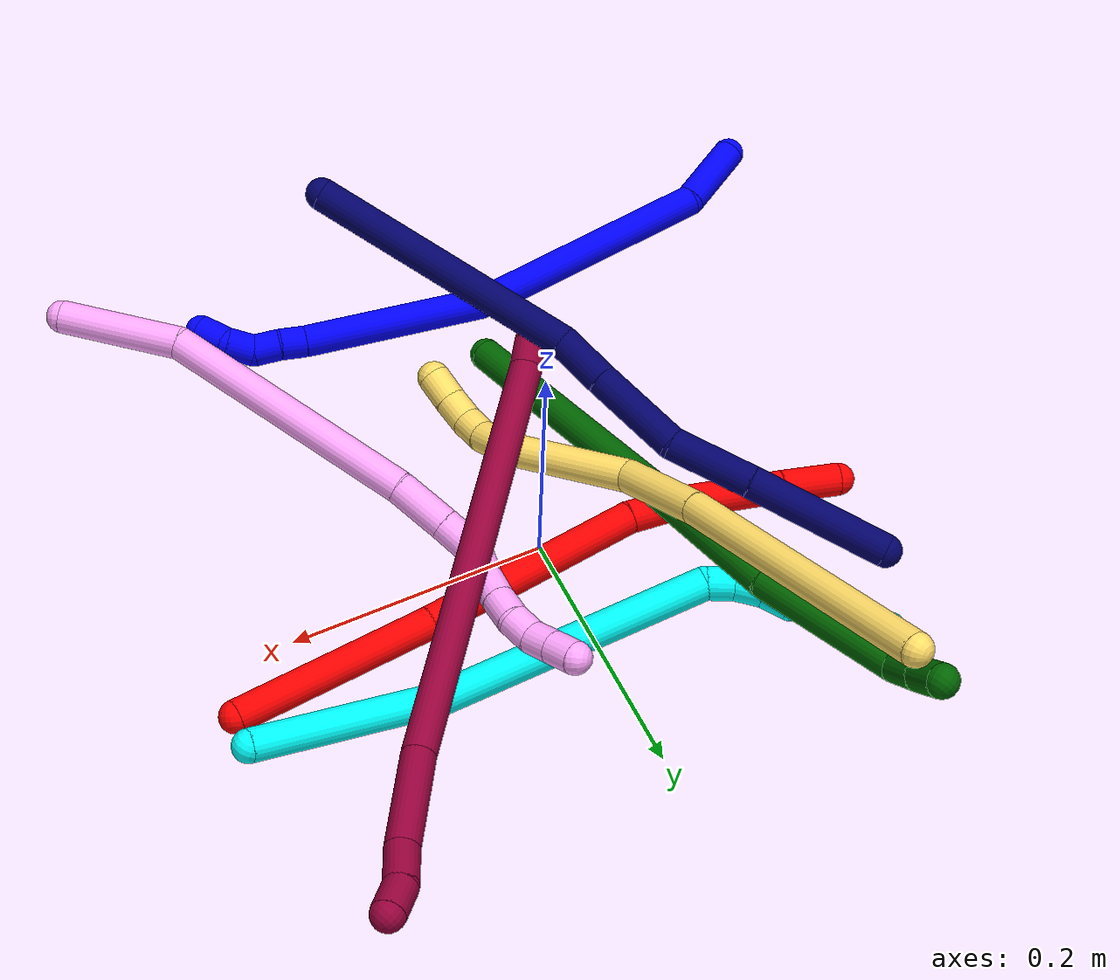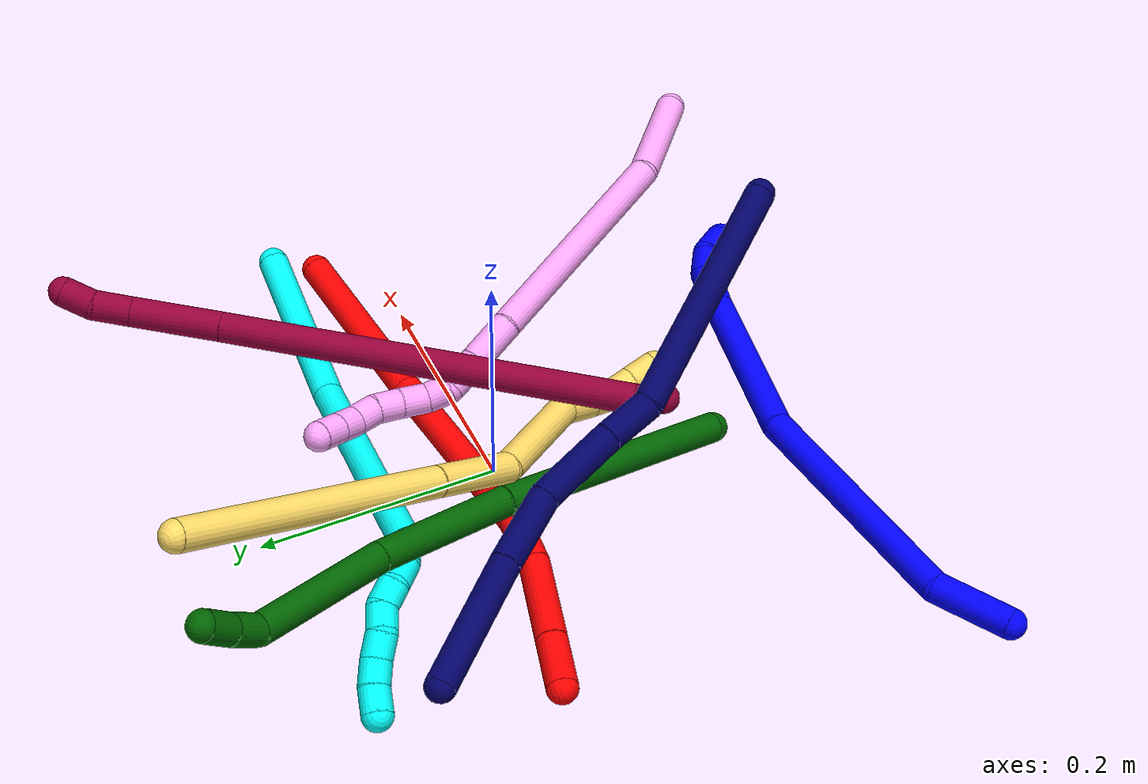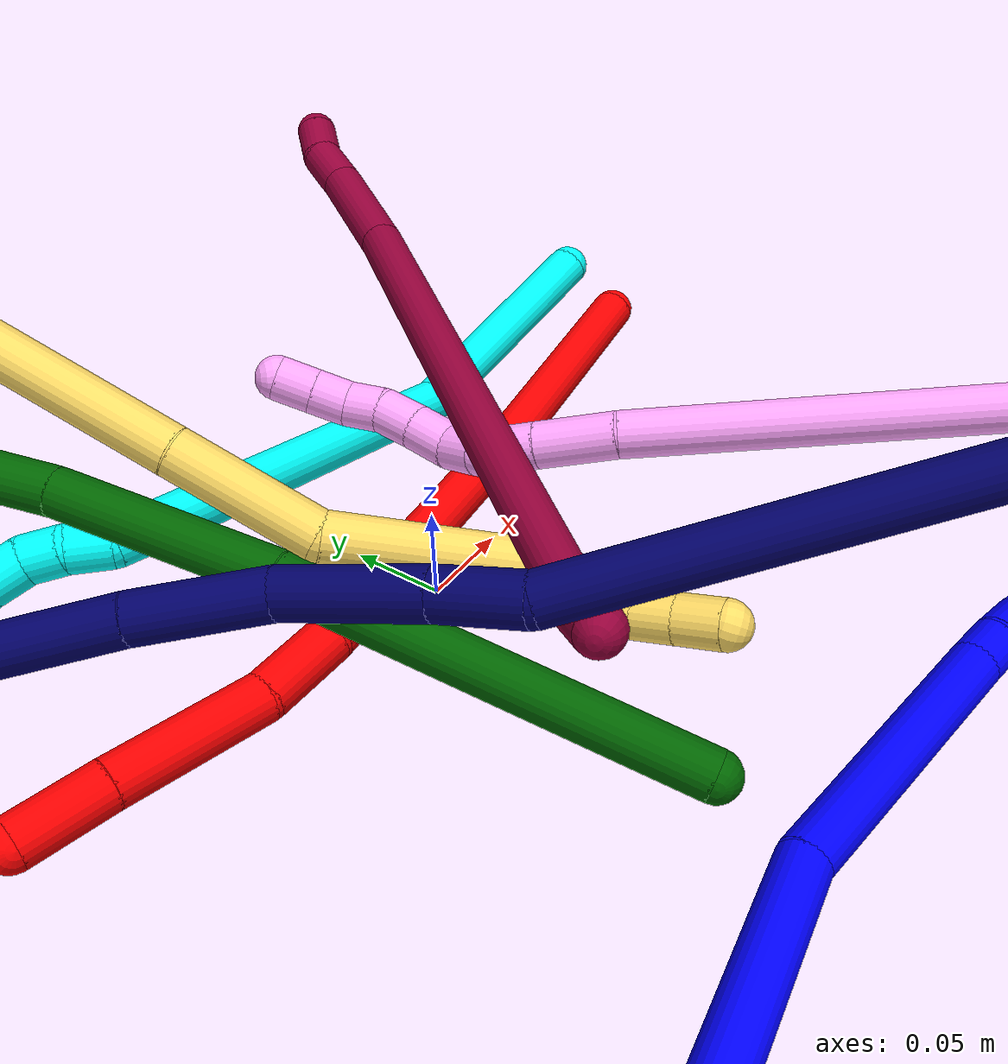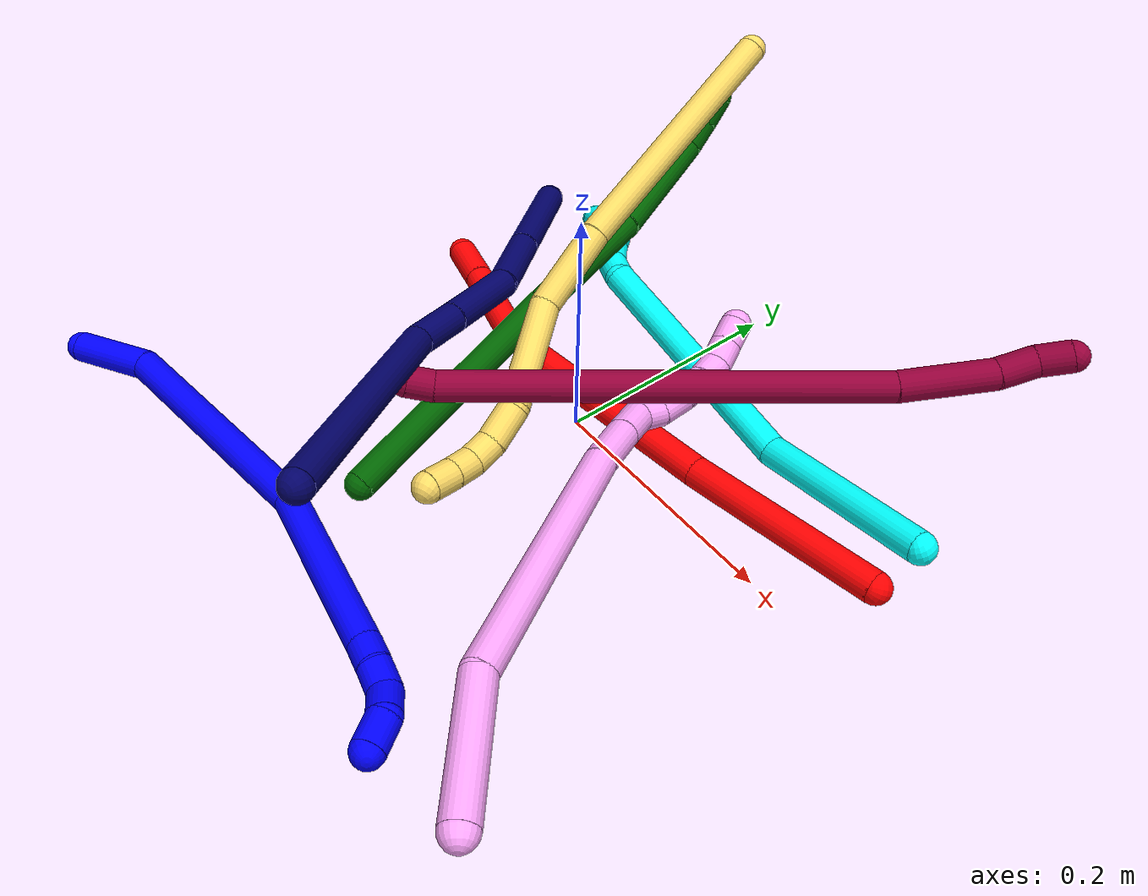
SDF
<sdf version="1.7">
 <world name="default">
  <plugin name="TubeGeneratorPlugin" filename="libtube_generator_plugin.so"/>
  <model name="photoneo_s_sensor">
   <static>1</static>
   <pose>0 0 2 1.57079 1.57079 3.14159</pose>
   <link name="link">
    <inertial><mass>0.1</mass></inertial>
    <sensor name="sensor" type="depth">
     <update_rate>30</update_rate>
     <camera>
      <horizontal_fov>1.22</horizontal_fov>
      <image><width>1920</width><height>1200</height><format>B8G8R8</format></image>
      <clip><near>0.1</near><far>4</far></clip>
      <depth_camera><output>points</output></depth_camera>
     </camera>
     <plugin name="camera_plugin" filename="libgazebo_ros_depth_camera.so">
      <baseline>0.2</baseline>
      <alwaysOn>1</alwaysOn>
      <updateRate>0.0</updateRate>
      <cameraName>camera_ir</cameraName>
      <imageTopicName>/camera/color/image_raw</imageTopicName>
      <cameraInfoTopicName>/camera/color/camera_info</cameraInfoTopicName>
      <depthImageTopicName>/camera/depth/image_raw</depthImageTopicName>
      <depthImageCameraInfoTopicName>/camera/depth/camera_info</depthImageCameraInfoTopicName>
      <pointCloudTopicName>/camera/depth/points</pointCloudTopicName>
      <frameName>fr_optical</frameName>
      <pointCloudCutoff>0.1</pointCloudCutoff>
      <pointCloudCutoffMax>2.0</pointCloudCutoffMax>
      <distortionK1>0</distortionK1>
      <distortionK2>0</distortionK2>
      <distortionK3>0</distortionK3>
      <distortionT1>0</distortionT1>
      <distortionT2>0</distortionT2>
      <CxPrime>0</CxPrime>
      <Cx>0</Cx>
      <Cy>0</Cy>
      <focalLength>0</focalLength>
      <hackBaseline>0</hackBaseline>
     </plugin>
    </sensor>
   </link>
  </model>
  <gravity>0 0 -9.8</gravity>
  <magnetic_field>6e-06 2.3e-05 -4.2e-05</magnetic_field>
  <atmosphere type="adiabatic"/>
  <physics name="default_physics" default="0" type="ode">
   <max_step_size>0.003</max_step_size>
   <real_time_factor>1</real_time_factor>
   <real_time_update_rate>1000</real_time_update_rate>
   <max_contacts>10000</max_contacts>
   <ode>
    <solver>
     <type>quick</type>
     <iters>100</iters>
     <sor>1.3</sor>
     <use_dynamic_moi_rescaling>0</use_dynamic_moi_rescaling>
    </solver>
    <constraints>
     <contact_max_correcting_vel>0</contact_max_correcting_vel>
     <contact_surface_layer>0.001</contact_surface_layer>
     <cfm>0</cfm>
     <erp>0.2</erp>
    </constraints>
   </ode>
  </physics>
  <scene><ambient>0.4 0.4 0.4 1</ambient><background>0.7 0.7 0.7 1</background><shadows>0</shadows></scene>
  <audio><device>default</device></audio>
  <spherical_coordinates>
   <surface_model>EARTH_WGS84</surface_model>
   <latitude_deg>0</latitude_deg>
   <longitude_deg>0</longitude_deg>
   <elevation>0</elevation>
   <heading_deg>0</heading_deg>
  </spherical_coordinates>
  <model name="bin">
   <static>1</static>
   <link name="bottom">
    <collision name="collision-bottom">
     <pose>0 0 -0.01 0 -0 0</pose>
     <geometry><box><size>0.8 0.6 0.02</size></box></geometry>
     <surface>
      <friction><ode><mu>100</mu><mu2>100</mu2></ode></friction>
      <contact><collide_bitmask>65535</collide_bitmask></contact>
     </surface>
    </collision>
   </link>
   <link name="west_wall">
    <collision name="collision-west_wall">
     <pose>-0.41 0 0.1 0 -0 0</pose>
     <geometry><box><size>0.02 0.6 0.2</size></box></geometry>
     <surface>
      <friction><ode><mu>100</mu><mu2>100</mu2></ode></friction>
      <contact><collide_bitmask>65535</collide_bitmask></contact>
     </surface>
    </collision>
   </link>
   <link name="east_wall">
    <collision name="collision-east_wall">
     <pose>0.41 0 0.1 0 -0 0</pose>
     <geometry><box><size>0.02 0.6 0.2</size></box></geometry>
     <surface>
      <friction><ode><mu>100</mu><mu2>100</mu2></ode></friction>
      <contact><collide_bitmask>65535</collide_bitmask></contact>
     </surface>
    </collision>
   </link>
   <link name="south_wall">
    <collision name="collision-south_wall">
     <pose>0 -0.31 0.1 0 -0 0</pose>
     <geometry><box><size>0.8 0.02 0.2</size></box></geometry>
     <surface>
      <friction><ode><mu>100</mu><mu2>100</mu2></ode></friction>
      <contact><collide_bitmask>65535</collide_bitmask></contact>
     </surface>
    </collision>
   </link>
   <link name="north_wall">
    <collision name="collision-north_wall">
     <pose>0 0.31 0.1 0 -0 0</pose>
     <geometry><box><size>0.8 0.02 0.2</size></box></geometry>
     <surface>
      <friction><ode><mu>100</mu><mu2>100</mu2></ode></friction>
      <contact><collide_bitmask>65535</collide_bitmask></contact>
     </surface>
    </collision>
   </link>
  </model>
  <model name="1">
   <static>0</static>
   <link name="1">
    <collision name="collision-cylinder-e_1_1_4">
     <pose>0.028662 -0.004553 -0.013015 2.80507 1.1224 2.61375</pose>
     <geometry><cylinder><radius>0.0125</radius><length>0.063613</length></cylinder></geometry>
     <surface>
      <friction><ode><mu>1.16</mu><mu2>1.16</mu2><slip1>0</slip1><slip2>0</slip2></ode></friction>
      <contact><ode><kp>1e+06</kp><kd>1</kd><max_vel>0</max_vel><min_depth>0.001</min_depth></ode></contact>
     </surface>
    </collision>
    <visual name="visual-cylinder-e_1_1_4">
     <pose>0.028662 -0.004553 -0.013015 2.80507 1.1224 2.61375</pose>
     <geometry><cylinder><radius>0.0125</radius><length>0.063613</length></cylinder></geometry>
     <material><ambient>0 0 1 1</ambient></material>
    </visual>
    <collision name="collision-cylinder-e_2_4_5">
     <pose>0.129143 -0.000375 -0.097504 -3.02004 0.784103 -2.84933</pose>
     <geometry><cylinder><radius>0.0125</radius><length>0.203397</length></cylinder></geometry>
     <surface>
      <friction><ode><mu>1.16</mu><mu2>1.16</mu2><slip1>0</slip1><slip2>0</slip2></ode></friction>
      <contact><ode><kp>1e+06</kp><kd>1</kd><max_vel>0</max_vel><min_depth>0.001</min_depth></ode></contact>
     </surface>
    </collision>
    <visual name="visual-cylinder-e_2_4_5">
     <pose>0.129143 -0.000375 -0.097504 -3.02004 0.784103 -2.84933</pose>
     <geometry><cylinder><radius>0.0125</radius><length>0.203397</length></cylinder></geometry>
     <material><ambient>0 0 1 1</ambient></material>
    </visual>
    <collision name="collision-cylinder-e_3_5_6">
     <pose>0.237179 0.023201 -0.230351 -2.90427 0.520765 -2.30009</pose>
     <geometry><cylinder><radius>0.0125</radius><length>0.145585</length></cylinder></geometry>
     <surface>
      <friction><ode><mu>1.16</mu><mu2>1.16</mu2><slip1>0</slip1><slip2>0</slip2></ode></friction>
      <contact><ode><kp>1e+06</kp><kd>1</kd><max_vel>0</max_vel><min_depth>0.001</min_depth></ode></contact>
     </surface>
    </collision>
    <visual name="visual-cylinder-e_3_5_6">
     <pose>0.237179 0.023201 -0.230351 -2.90427 0.520765 -2.30009</pose>
     <geometry><cylinder><radius>0.0125</radius><length>0.145585</length></cylinder></geometry>
     <material><ambient>0 0 1 1</ambient></material>
    </visual>
    <collision name="collision-cylinder-e_4_6_7">
     <pose>0.277712 0.039629 -0.300668 -2.96639 0.44361 -2.39884</pose>
     <geometry><cylinder><radius>0.0125</radius><length>0.020112</length></cylinder></geometry>
     <surface>
      <friction><ode><mu>1.16</mu><mu2>1.16</mu2><slip1>0</slip1><slip2>0</slip2></ode></friction>
      <contact><ode><kp>1e+06</kp><kd>1</kd><max_vel>0</max_vel><min_depth>0.001</min_depth></ode></contact>
     </surface>
    </collision>
    <visual name="visual-cylinder-e_4_6_7">
     <pose>0.277712 0.039629 -0.300668 -2.96639 0.44361 -2.39884</pose>
     <geometry><cylinder><radius>0.0125</radius><length>0.020112</length></cylinder></geometry>
     <material><ambient>0 0 1 1</ambient></material>
    </visual>
    <collision name="collision-cylinder-e_5_7_8">
     <pose>0.287066 0.044408 -0.318202 -2.7854 0.502524 -1.91846</pose>
     <geometry><cylinder><radius>0.0125</radius><length>0.020918</length></cylinder></geometry>
     <surface>
      <friction><ode><mu>1.16</mu><mu2>1.16</mu2><slip1>0</slip1><slip2>0</slip2></ode></friction>
      <contact><ode><kp>1e+06</kp><kd>1</kd><max_vel>0</max_vel><min_depth>0.001</min_depth></ode></contact>
     </surface>
    </collision>
    <visual name="visual-cylinder-e_5_7_8">
     <pose>0.287066 0.044408 -0.318202 -2.7854 0.502524 -1.91846</pose>
     <geometry><cylinder><radius>0.0125</radius><length>0.020918</length></cylinder></geometry>
     <material><ambient>0 0 1 1</ambient></material>
    </visual>
    <collision name="collision-cylinder-e_6_8_9">
     <pose>0.292565 0.04904 -0.337888 -3.01295 0.041285 -0.620359</pose>
     <geometry><cylinder><radius>0.0125</radius><length>0.022394</length></cylinder></geometry>
     <surface>
      <friction><ode><mu>1.16</mu><mu2>1.16</mu2><slip1>0</slip1><slip2>0</slip2></ode></friction>
      <contact><ode><kp>1e+06</kp><kd>1</kd><max_vel>0</max_vel><min_depth>0.001</min_depth></ode></contact>
     </surface>
    </collision>
    <visual name="visual-cylinder-e_6_8_9">
     <pose>0.292565 0.04904 -0.337888 -3.01295 0.041285 -0.620359</pose>
     <geometry><cylinder><radius>0.0125</radius><length>0.022394</length></cylinder></geometry>
     <material><ambient>0 0 1 1</ambient></material>
    </visual>
    <collision name="collision-cylinder-e_7_9_2">
     <pose>0.290002 0.056523 -0.358885 -2.59327 -0.255106 0.855684</pose>
     <geometry><cylinder><radius>0.0125</radius><length>0.023981</length></cylinder></geometry>
     <surface>
      <friction><ode><mu>1.16</mu><mu2>1.16</mu2><slip1>0</slip1><slip2>0</slip2></ode></friction>
      <contact><ode><kp>1e+06</kp><kd>1</kd><max_vel>0</max_vel><min_depth>0.001</min_depth></ode></contact>
     </surface>
    </collision>
    <visual name="visual-cylinder-e_7_9_2">
     <pose>0.290002 0.056523 -0.358885 -2.59327 -0.255106 0.855684</pose>
     <geometry><cylinder><radius>0.0125</radius><length>0.023981</length></cylinder></geometry>
     <material><ambient>0 0 1 1</ambient></material>
    </visual>
    <collision name="collision-sphere-2">
     <pose>0.286976 0.062571 -0.368786 0 -0 0</pose>
     <geometry><sphere><radius>0.0125</radius></sphere></geometry>
     <surface>
      <friction><ode><mu>1.16</mu><mu2>1.16</mu2><slip1>0</slip1><slip2>0</slip2></ode></friction>
      <contact><ode><kp>1e+06</kp><kd>1</kd><max_vel>0</max_vel><min_depth>0.001</min_depth></ode></contact>
     </surface>
    </collision>
    <visual name="visual-sphere-2">
     <pose>0.286976 0.062571 -0.368786 0 -0 0</pose>
     <geometry><sphere><radius>0.0125</radius></sphere></geometry>
     <material><ambient>0 0 1 1</ambient></material>
    </visual>
    <collision name="collision-sphere-9">
     <pose>0.293027 0.050475 -0.348983 0 -0 0</pose>
     <geometry><sphere><radius>0.0125</radius></sphere></geometry>
     <surface>
      <friction><ode><mu>1.16</mu><mu2>1.16</mu2><slip1>0</slip1><slip2>0</slip2></ode></friction>
      <contact><ode><kp>1e+06</kp><kd>1</kd><max_vel>0</max_vel><min_depth>0.001</min_depth></ode></contact>
     </surface>
    </collision>
    <visual name="visual-sphere-9">
     <pose>0.293027 0.050475 -0.348983 0 -0 0</pose>
     <geometry><sphere><radius>0.0125</radius></sphere></geometry>
     <material><ambient>0 0 1 1</ambient></material>
    </visual>
    <collision name="collision-sphere-4">
     <pose>0.057324 -0.009106 -0.026031 0 -0 0</pose>
     <geometry><sphere><radius>0.0125</radius></sphere></geometry>
     <surface>
      <friction><ode><mu>1.16</mu><mu2>1.16</mu2><slip1>0</slip1><slip2>0</slip2></ode></friction>
      <contact><ode><kp>1e+06</kp><kd>1</kd><max_vel>0</max_vel><min_depth>0.001</min_depth></ode></contact>
     </surface>
    </collision>
    <visual name="visual-sphere-4">
     <pose>0.057324 -0.009106 -0.026031 0 -0 0</pose>
     <geometry><sphere><radius>0.0125</radius></sphere></geometry>
     <material><ambient>0 0 1 1</ambient></material>
    </visual>
    <collision name="collision-sphere-1">
     <geometry><sphere><radius>0.0125</radius></sphere></geometry>
     <surface>
      <friction><ode><mu>1.16</mu><mu2>1.16</mu2><slip1>0</slip1><slip2>0</slip2></ode></friction>
      <contact><ode><kp>1e+06</kp><kd>1</kd><max_vel>0</max_vel><min_depth>0.001</min_depth></ode></contact>
     </surface>
    </collision>
    <visual name="visual-sphere-1">
     <geometry><sphere><radius>0.0125</radius></sphere></geometry>
     <material><ambient>0 0 1 1</ambient></material>
    </visual>
    <collision name="collision-sphere-8">
     <pose>0.292103 0.047604 -0.326793 0 -0 0</pose>
     <geometry><sphere><radius>0.0125</radius></sphere></geometry>
     <surface>
      <friction><ode><mu>1.16</mu><mu2>1.16</mu2><slip1>0</slip1><slip2>0</slip2></ode></friction>
      <contact><ode><kp>1e+06</kp><kd>1</kd><max_vel>0</max_vel><min_depth>0.001</min_depth></ode></contact>
     </surface>
    </collision>
    <visual name="visual-sphere-8">
     <pose>0.292103 0.047604 -0.326793 0 -0 0</pose>
     <geometry><sphere><radius>0.0125</radius></sphere></geometry>
     <material><ambient>0 0 1 1</ambient></material>
    </visual>
    <collision name="collision-sphere-5">
     <pose>0.200961 0.008356 -0.168978 0 -0 0</pose>
     <geometry><sphere><radius>0.0125</radius></sphere></geometry>
     <surface>
      <friction><ode><mu>1.16</mu><mu2>1.16</mu2><slip1>0</slip1><slip2>0</slip2></ode></friction>
      <contact><ode><kp>1e+06</kp><kd>1</kd><max_vel>0</max_vel><min_depth>0.001</min_depth></ode></contact>
     </surface>
    </collision>
    <visual name="visual-sphere-5">
     <pose>0.200961 0.008356 -0.168978 0 -0 0</pose>
     <geometry><sphere><radius>0.0125</radius></sphere></geometry>
     <material><ambient>0 0 1 1</ambient></material>
    </visual>
    <collision name="collision-sphere-6">
     <pose>0.273396 0.038046 -0.291724 0 -0 0</pose>
     <geometry><sphere><radius>0.0125</radius></sphere></geometry>
     <surface>
      <friction><ode><mu>1.16</mu><mu2>1.16</mu2><slip1>0</slip1><slip2>0</slip2></ode></friction>
      <contact><ode><kp>1e+06</kp><kd>1</kd><max_vel>0</max_vel><min_depth>0.001</min_depth></ode></contact>
     </surface>
    </collision>
    <visual name="visual-sphere-6">
     <pose>0.273396 0.038046 -0.291724 0 -0 0</pose>
     <geometry><sphere><radius>0.0125</radius></sphere></geometry>
     <material><ambient>0 0 1 1</ambient></material>
    </visual>
    <collision name="collision-sphere-7">
     <pose>0.282028 0.041212 -0.309611 0 -0 0</pose>
     <geometry><sphere><radius>0.0125</radius></sphere></geometry>
     <surface>
      <friction><ode><mu>1.16</mu><mu2>1.16</mu2><slip1>0</slip1><slip2>0</slip2></ode></friction>
      <contact><ode><kp>1e+06</kp><kd>1</kd><max_vel>0</max_vel><min_depth>0.001</min_depth></ode></contact>
     </surface>
    </collision>
    <visual name="visual-sphere-7">
     <pose>0.282028 0.041212 -0.309611 0 -0 0</pose>
     <geometry><sphere><radius>0.0125</radius></sphere></geometry>
     <material><ambient>0 0 1 1</ambient></material>
    </visual>
    <inertial>
     <pose>0.175433 0.014383 -0.166144 0 -0 0</pose>
     <mass>0.5</mass>
     <inertia>
      <ixx>-0.000929</ixx>
      <ixy>0</ixy>
      <ixz>0</ixz>
      <iyy>0.000601</iyy>
      <iyz>0</iyz>
      <izz>-0.000796</izz>
     </inertia>
    </inertial>
   </link>
   <pose>-0.313235 -0.288502 0.014056 -2.0195 0.328402 0.867038</pose>
  </model>
  <model name="2">
   <static>0</static>
   <link name="2">
    <collision name="collision-cylinder-e_1_1_4">
     <pose>-0.073983 0.004055 0.030953 -0.130257 -1.17151 0.086484</pose>
     <geometry><cylinder><radius>0.0125</radius><length>0.160598</length></cylinder></geometry>
     <surface>
      <friction><ode><mu>1.16</mu><mu2>1.16</mu2><slip1>0</slip1><slip2>0</slip2></ode></friction>
      <contact><ode><kp>1e+06</kp><kd>1</kd><max_vel>0</max_vel><min_depth>0.001</min_depth></ode></contact>
     </surface>
    </collision>
    <visual name="visual-cylinder-e_1_1_4">
     <pose>-0.073983 0.004055 0.030953 -0.130257 -1.17151 0.086484</pose>
     <geometry><cylinder><radius>0.0125</radius><length>0.160598</length></cylinder></geometry>
     <material><ambient>1 0 0 1</ambient></material>
    </visual>
    <collision name="collision-cylinder-e_2_4_5">
     <pose>-0.226274 0.018034 0.098708 -0.26341 -1.11781 0.165324</pose>
     <geometry><cylinder><radius>0.0125</radius><length>0.174186</length></cylinder></geometry>
     <surface>
      <friction><ode><mu>1.16</mu><mu2>1.16</mu2><slip1>0</slip1><slip2>0</slip2></ode></friction>
      <contact><ode><kp>1e+06</kp><kd>1</kd><max_vel>0</max_vel><min_depth>0.001</min_depth></ode></contact>
     </surface>
    </collision>
    <visual name="visual-cylinder-e_2_4_5">
     <pose>-0.226274 0.018034 0.098708 -0.26341 -1.11781 0.165324</pose>
     <geometry><cylinder><radius>0.0125</radius><length>0.174186</length></cylinder></geometry>
     <material><ambient>1 0 0 1</ambient></material>
    </visual>
    <collision name="collision-cylinder-e_3_5_6">
     <pose>-0.325542 0.031269 0.140704 -0.567394 -1.28497 0.42968</pose>
     <geometry><cylinder><radius>0.0125</radius><length>0.043692</length></cylinder></geometry>
     <surface>
      <friction><ode><mu>1.16</mu><mu2>1.16</mu2><slip1>0</slip1><slip2>0</slip2></ode></friction>
      <contact><ode><kp>1e+06</kp><kd>1</kd><max_vel>0</max_vel><min_depth>0.001</min_depth></ode></contact>
     </surface>
    </collision>
    <visual name="visual-cylinder-e_3_5_6">
     <pose>-0.325542 0.031269 0.140704 -0.567394 -1.28497 0.42968</pose>
     <geometry><cylinder><radius>0.0125</radius><length>0.043692</length></cylinder></geometry>
     <material><ambient>1 0 0 1</ambient></material>
    </visual>
    <collision name="collision-cylinder-e_4_6_7">
     <pose>-0.382851 0.047138 0.150398 -1.22678 -1.21905 0.913696</pose>
     <geometry><cylinder><radius>0.0125</radius><length>0.077439</length></cylinder></geometry>
     <surface>
      <friction><ode><mu>1.16</mu><mu2>1.16</mu2><slip1>0</slip1><slip2>0</slip2></ode></friction>
      <contact><ode><kp>1e+06</kp><kd>1</kd><max_vel>0</max_vel><min_depth>0.001</min_depth></ode></contact>
     </surface>
    </collision>
    <visual name="visual-cylinder-e_4_6_7">
     <pose>-0.382851 0.047138 0.150398 -1.22678 -1.21905 0.913696</pose>
     <geometry><cylinder><radius>0.0125</radius><length>0.077439</length></cylinder></geometry>
     <material><ambient>1 0 0 1</ambient></material>
    </visual>
    <collision name="collision-cylinder-e_5_7_2">
     <pose>-0.440227 0.065959 0.157019 -1.2441 -1.26614 0.968708</pose>
     <geometry><cylinder><radius>0.0125</radius><length>0.044085</length></cylinder></geometry>
     <surface>
      <friction><ode><mu>1.16</mu><mu2>1.16</mu2><slip1>0</slip1><slip2>0</slip2></ode></friction>
      <contact><ode><kp>1e+06</kp><kd>1</kd><max_vel>0</max_vel><min_depth>0.001</min_depth></ode></contact>
     </surface>
    </collision>
    <visual name="visual-cylinder-e_5_7_2">
     <pose>-0.440227 0.065959 0.157019 -1.2441 -1.26614 0.968708</pose>
     <geometry><cylinder><radius>0.0125</radius><length>0.044085</length></cylinder></geometry>
     <material><ambient>1 0 0 1</ambient></material>
    </visual>
    <collision name="collision-sphere-2">
     <pose>-0.461255 0.072221 0.159141 0 -0 0</pose>
     <geometry><sphere><radius>0.0125</radius></sphere></geometry>
     <surface>
      <friction><ode><mu>1.16</mu><mu2>1.16</mu2><slip1>0</slip1><slip2>0</slip2></ode></friction>
      <contact><ode><kp>1e+06</kp><kd>1</kd><max_vel>0</max_vel><min_depth>0.001</min_depth></ode></contact>
     </surface>
    </collision>
    <visual name="visual-sphere-2">
     <pose>-0.461255 0.072221 0.159141 0 -0 0</pose>
     <geometry><sphere><radius>0.0125</radius></sphere></geometry>
     <material><ambient>1 0 0 1</ambient></material>
    </visual>
    <collision name="collision-sphere-7">
     <pose>-0.4192 0.059697 0.154897 0 -0 0</pose>
     <geometry><sphere><radius>0.0125</radius></sphere></geometry>
     <surface>
      <friction><ode><mu>1.16</mu><mu2>1.16</mu2><slip1>0</slip1><slip2>0</slip2></ode></friction>
      <contact><ode><kp>1e+06</kp><kd>1</kd><max_vel>0</max_vel><min_depth>0.001</min_depth></ode></contact>
     </surface>
    </collision>
    <visual name="visual-sphere-7">
     <pose>-0.4192 0.059697 0.154897 0 -0 0</pose>
     <geometry><sphere><radius>0.0125</radius></sphere></geometry>
     <material><ambient>1 0 0 1</ambient></material>
    </visual>
    <collision name="collision-sphere-6">
     <pose>-0.346502 0.03458 0.145899 0 -0 0</pose>
     <geometry><sphere><radius>0.0125</radius></sphere></geometry>
     <surface>
      <friction><ode><mu>1.16</mu><mu2>1.16</mu2><slip1>0</slip1><slip2>0</slip2></ode></friction>
      <contact><ode><kp>1e+06</kp><kd>1</kd><max_vel>0</max_vel><min_depth>0.001</min_depth></ode></contact>
     </surface>
    </collision>
    <visual name="visual-sphere-6">
     <pose>-0.346502 0.03458 0.145899 0 -0 0</pose>
     <geometry><sphere><radius>0.0125</radius></sphere></geometry>
     <material><ambient>1 0 0 1</ambient></material>
    </visual>
    <collision name="collision-sphere-5">
     <pose>-0.304583 0.027959 0.13551 0 -0 0</pose>
     <geometry><sphere><radius>0.0125</radius></sphere></geometry>
     <surface>
      <friction><ode><mu>1.16</mu><mu2>1.16</mu2><slip1>0</slip1><slip2>0</slip2></ode></friction>
      <contact><ode><kp>1e+06</kp><kd>1</kd><max_vel>0</max_vel><min_depth>0.001</min_depth></ode></contact>
     </surface>
    </collision>
    <visual name="visual-sphere-5">
     <pose>-0.304583 0.027959 0.13551 0 -0 0</pose>
     <geometry><sphere><radius>0.0125</radius></sphere></geometry>
     <material><ambient>1 0 0 1</ambient></material>
    </visual>
    <collision name="collision-sphere-1">
     <geometry><sphere><radius>0.0125</radius></sphere></geometry>
     <surface>
      <friction><ode><mu>1.16</mu><mu2>1.16</mu2><slip1>0</slip1><slip2>0</slip2></ode></friction>
      <contact><ode><kp>1e+06</kp><kd>1</kd><max_vel>0</max_vel><min_depth>0.001</min_depth></ode></contact>
     </surface>
    </collision>
    <visual name="visual-sphere-1">
     <geometry><sphere><radius>0.0125</radius></sphere></geometry>
     <material><ambient>1 0 0 1</ambient></material>
    </visual>
    <collision name="collision-sphere-4">
     <pose>-0.147965 0.00811 0.061906 0 -0 0</pose>
     <geometry><sphere><radius>0.0125</radius></sphere></geometry>
     <surface>
      <friction><ode><mu>1.16</mu><mu2>1.16</mu2><slip1>0</slip1><slip2>0</slip2></ode></friction>
      <contact><ode><kp>1e+06</kp><kd>1</kd><max_vel>0</max_vel><min_depth>0.001</min_depth></ode></contact>
     </surface>
    </collision>
    <visual name="visual-sphere-4">
     <pose>-0.147965 0.00811 0.061906 0 -0 0</pose>
     <geometry><sphere><radius>0.0125</radius></sphere></geometry>
     <material><ambient>1 0 0 1</ambient></material>
    </visual>
    <inertial>
     <pose>-0.229148 0.023434 0.093762 0 -0 0</pose>
     <mass>0.5</mass>
     <inertia>
      <ixx>0.000364</ixx>
      <ixy>0</ixy>
      <ixz>0</ixz>
      <iyy>0.000913</iyy>
      <iyz>0</iyz>
      <izz>0.000708</izz>
     </inertia>
    </inertial>
   </link>
   <pose>0.264307 0.05307 0.020356 0.99081 -0.326242 -0.174027</pose>
  </model>
  <model name="3">
   <static>0</static>
   <link name="3">
    <collision name="collision-cylinder-e_1_1_4">
     <pose>-0.065872 0.022811 -0.021089 -2.31697 -1.13012 1.93382</pose>
     <geometry><cylinder><radius>0.0125</radius><length>0.14566</length></cylinder></geometry>
     <surface>
      <friction><ode><mu>1.16</mu><mu2>1.16</mu2><slip1>0</slip1><slip2>0</slip2></ode></friction>
      <contact><ode><kp>1e+06</kp><kd>1</kd><max_vel>0</max_vel><min_depth>0.001</min_depth></ode></contact>
     </surface>
    </collision>
    <visual name="visual-cylinder-e_1_1_4">
     <pose>-0.065872 0.022811 -0.021089 -2.31697 -1.13012 1.93382</pose>
     <geometry><cylinder><radius>0.0125</radius><length>0.14566</length></cylinder></geometry>
     <material><ambient>0.003922 1 0.996078 1</ambient></material>
    </visual>
    <collision name="collision-cylinder-e_2_4_5">
     <pose>-0.211705 0.063844 -0.105534 -2.86156 -0.881321 2.56077</pose>
     <geometry><cylinder><radius>0.0125</radius><length>0.207266</length></cylinder></geometry>
     <surface>
      <friction><ode><mu>1.16</mu><mu2>1.16</mu2><slip1>0</slip1><slip2>0</slip2></ode></friction>
      <contact><ode><kp>1e+06</kp><kd>1</kd><max_vel>0</max_vel><min_depth>0.001</min_depth></ode></contact>
     </surface>
    </collision>
    <visual name="visual-cylinder-e_2_4_5">
     <pose>-0.211705 0.063844 -0.105534 -2.86156 -0.881321 2.56077</pose>
     <geometry><cylinder><radius>0.0125</radius><length>0.207266</length></cylinder></geometry>
     <material><ambient>0.003922 1 0.996078 1</ambient></material>
    </visual>
    <collision name="collision-cylinder-e_3_5_6">
     <pose>-0.301978 0.081331 -0.172313 2.93065 -1.24353 -2.84823</pose>
     <geometry><cylinder><radius>0.0125</radius><length>0.02178</length></cylinder></geometry>
     <surface>
      <friction><ode><mu>1.16</mu><mu2>1.16</mu2><slip1>0</slip1><slip2>0</slip2></ode></friction>
      <contact><ode><kp>1e+06</kp><kd>1</kd><max_vel>0</max_vel><min_depth>0.001</min_depth></ode></contact>
     </surface>
    </collision>
    <visual name="visual-cylinder-e_3_5_6">
     <pose>-0.301978 0.081331 -0.172313 2.93065 -1.24353 -2.84823</pose>
     <geometry><cylinder><radius>0.0125</radius><length>0.02178</length></cylinder></geometry>
     <material><ambient>0.003922 1 0.996078 1</ambient></material>
    </visual>
    <collision name="collision-cylinder-e_4_6_7">
     <pose>-0.321855 0.076083 -0.178778 2.1637 -1.0533 -1.65945</pose>
     <geometry><cylinder><radius>0.0125</radius><length>0.022011</length></cylinder></geometry>
     <surface>
      <friction><ode><mu>1.16</mu><mu2>1.16</mu2><slip1>0</slip1><slip2>0</slip2></ode></friction>
      <contact><ode><kp>1e+06</kp><kd>1</kd><max_vel>0</max_vel><min_depth>0.001</min_depth></ode></contact>
     </surface>
    </collision>
    <visual name="visual-cylinder-e_4_6_7">
     <pose>-0.321855 0.076083 -0.178778 2.1637 -1.0533 -1.65945</pose>
     <geometry><cylinder><radius>0.0125</radius><length>0.022011</length></cylinder></geometry>
     <material><ambient>0.003922 1 0.996078 1</ambient></material>
    </visual>
    <collision name="collision-cylinder-e_5_7_8">
     <pose>-0.340673 0.067451 -0.181784 1.56202 -1.15224 -1.14423</pose>
     <geometry><cylinder><radius>0.0125</radius><length>0.020257</length></cylinder></geometry>
     <surface>
      <friction><ode><mu>1.16</mu><mu2>1.16</mu2><slip1>0</slip1><slip2>0</slip2></ode></friction>
      <contact><ode><kp>1e+06</kp><kd>1</kd><max_vel>0</max_vel><min_depth>0.001</min_depth></ode></contact>
     </surface>
    </collision>
    <visual name="visual-cylinder-e_5_7_8">
     <pose>-0.340673 0.067451 -0.181784 1.56202 -1.15224 -1.14423</pose>
     <geometry><cylinder><radius>0.0125</radius><length>0.020257</length></cylinder></geometry>
     <material><ambient>0.003922 1 0.996078 1</ambient></material>
    </visual>
    <collision name="collision-cylinder-e_6_8_9">
     <pose>-0.36011 0.063535 -0.183057 -2.99026 -1.44153 2.96941</pose>
     <geometry><cylinder><radius>0.0125</radius><length>0.020538</length></cylinder></geometry>
     <surface>
      <friction><ode><mu>1.16</mu><mu2>1.16</mu2><slip1>0</slip1><slip2>0</slip2></ode></friction>
      <contact><ode><kp>1e+06</kp><kd>1</kd><max_vel>0</max_vel><min_depth>0.001</min_depth></ode></contact>
     </surface>
    </collision>
    <visual name="visual-cylinder-e_6_8_9">
     <pose>-0.36011 0.063535 -0.183057 -2.99026 -1.44153 2.96941</pose>
     <geometry><cylinder><radius>0.0125</radius><length>0.020538</length></cylinder></geometry>
     <material><ambient>0.003922 1 0.996078 1</ambient></material>
    </visual>
    <collision name="collision-cylinder-e_7_9_10">
     <pose>-0.380418 0.062607 -0.182379 0.516367 -1.34896 -0.416183</pose>
     <geometry><cylinder><radius>0.0125</radius><length>0.020758</length></cylinder></geometry>
     <surface>
      <friction><ode><mu>1.16</mu><mu2>1.16</mu2><slip1>0</slip1><slip2>0</slip2></ode></friction>
      <contact><ode><kp>1e+06</kp><kd>1</kd><max_vel>0</max_vel><min_depth>0.001</min_depth></ode></contact>
     </surface>
    </collision>
    <visual name="visual-cylinder-e_7_9_10">
     <pose>-0.380418 0.062607 -0.182379 0.516367 -1.34896 -0.416183</pose>
     <geometry><cylinder><radius>0.0125</radius><length>0.020758</length></cylinder></geometry>
     <material><ambient>0.003922 1 0.996078 1</ambient></material>
    </visual>
    <collision name="collision-cylinder-e_8_10_11">
     <pose>-0.400627 0.061244 -0.18001 0.549982 -1.52619 -0.527102</pose>
     <geometry><cylinder><radius>0.0125</radius><length>0.020189</length></cylinder></geometry>
     <surface>
      <friction><ode><mu>1.16</mu><mu2>1.16</mu2><slip1>0</slip1><slip2>0</slip2></ode></friction>
      <contact><ode><kp>1e+06</kp><kd>1</kd><max_vel>0</max_vel><min_depth>0.001</min_depth></ode></contact>
     </surface>
    </collision>
    <visual name="visual-cylinder-e_8_10_11">
     <pose>-0.400627 0.061244 -0.18001 0.549982 -1.52619 -0.527102</pose>
     <geometry><cylinder><radius>0.0125</radius><length>0.020189</length></cylinder></geometry>
     <material><ambient>0.003922 1 0.996078 1</ambient></material>
    </visual>
    <collision name="collision-cylinder-e_9_11_2">
     <pose>-0.421316 0.062739 -0.180375 -1.97948 -1.39486 1.81213</pose>
     <geometry><cylinder><radius>0.0125</radius><length>0.021541</length></cylinder></geometry>
     <surface>
      <friction><ode><mu>1.16</mu><mu2>1.16</mu2><slip1>0</slip1><slip2>0</slip2></ode></friction>
      <contact><ode><kp>1e+06</kp><kd>1</kd><max_vel>0</max_vel><min_depth>0.001</min_depth></ode></contact>
     </surface>
    </collision>
    <visual name="visual-cylinder-e_9_11_2">
     <pose>-0.421316 0.062739 -0.180375 -1.97948 -1.39486 1.81213</pose>
     <geometry><cylinder><radius>0.0125</radius><length>0.021541</length></cylinder></geometry>
     <material><ambient>0.003922 1 0.996078 1</ambient></material>
    </visual>
    <collision name="collision-sphere-2">
     <pose>-0.431921 0.064468 -0.181124 0 -0 0</pose>
     <geometry><sphere><radius>0.0125</radius></sphere></geometry>
     <surface>
      <friction><ode><mu>1.16</mu><mu2>1.16</mu2><slip1>0</slip1><slip2>0</slip2></ode></friction>
      <contact><ode><kp>1e+06</kp><kd>1</kd><max_vel>0</max_vel><min_depth>0.001</min_depth></ode></contact>
     </surface>
    </collision>
    <visual name="visual-sphere-2">
     <pose>-0.431921 0.064468 -0.181124 0 -0 0</pose>
     <geometry><sphere><radius>0.0125</radius></sphere></geometry>
     <material><ambient>0.003922 1 0.996078 1</ambient></material>
    </visual>
    <collision name="collision-sphere-11">
     <pose>-0.410712 0.061009 -0.179626 0 -0 0</pose>
     <geometry><sphere><radius>0.0125</radius></sphere></geometry>
     <surface>
      <friction><ode><mu>1.16</mu><mu2>1.16</mu2><slip1>0</slip1><slip2>0</slip2></ode></friction>
      <contact><ode><kp>1e+06</kp><kd>1</kd><max_vel>0</max_vel><min_depth>0.001</min_depth></ode></contact>
     </surface>
    </collision>
    <visual name="visual-sphere-11">
     <pose>-0.410712 0.061009 -0.179626 0 -0 0</pose>
     <geometry><sphere><radius>0.0125</radius></sphere></geometry>
     <material><ambient>0.003922 1 0.996078 1</ambient></material>
    </visual>
    <collision name="collision-sphere-10">
     <pose>-0.390543 0.061479 -0.180394 0 -0 0</pose>
     <geometry><sphere><radius>0.0125</radius></sphere></geometry>
     <surface>
      <friction><ode><mu>1.16</mu><mu2>1.16</mu2><slip1>0</slip1><slip2>0</slip2></ode></friction>
      <contact><ode><kp>1e+06</kp><kd>1</kd><max_vel>0</max_vel><min_depth>0.001</min_depth></ode></contact>
     </surface>
    </collision>
    <visual name="visual-sphere-10">
     <pose>-0.390543 0.061479 -0.180394 0 -0 0</pose>
     <geometry><sphere><radius>0.0125</radius></sphere></geometry>
     <material><ambient>0.003922 1 0.996078 1</ambient></material>
    </visual>
    <collision name="collision-sphere-9">
     <pose>-0.370294 0.063734 -0.184365 0 -0 0</pose>
     <geometry><sphere><radius>0.0125</radius></sphere></geometry>
     <surface>
      <friction><ode><mu>1.16</mu><mu2>1.16</mu2><slip1>0</slip1><slip2>0</slip2></ode></friction>
      <contact><ode><kp>1e+06</kp><kd>1</kd><max_vel>0</max_vel><min_depth>0.001</min_depth></ode></contact>
     </surface>
    </collision>
    <visual name="visual-sphere-9">
     <pose>-0.370294 0.063734 -0.184365 0 -0 0</pose>
     <geometry><sphere><radius>0.0125</radius></sphere></geometry>
     <material><ambient>0.003922 1 0.996078 1</ambient></material>
    </visual>
    <collision name="collision-sphere-4">
     <pose>-0.131744 0.045623 -0.042177 0 -0 0</pose>
     <geometry><sphere><radius>0.0125</radius></sphere></geometry>
     <surface>
      <friction><ode><mu>1.16</mu><mu2>1.16</mu2><slip1>0</slip1><slip2>0</slip2></ode></friction>
      <contact><ode><kp>1e+06</kp><kd>1</kd><max_vel>0</max_vel><min_depth>0.001</min_depth></ode></contact>
     </surface>
    </collision>
    <visual name="visual-sphere-4">
     <pose>-0.131744 0.045623 -0.042177 0 -0 0</pose>
     <geometry><sphere><radius>0.0125</radius></sphere></geometry>
     <material><ambient>0.003922 1 0.996078 1</ambient></material>
    </visual>
    <collision name="collision-sphere-1">
     <geometry><sphere><radius>0.0125</radius></sphere></geometry>
     <surface>
      <friction><ode><mu>1.16</mu><mu2>1.16</mu2><slip1>0</slip1><slip2>0</slip2></ode></friction>
      <contact><ode><kp>1e+06</kp><kd>1</kd><max_vel>0</max_vel><min_depth>0.001</min_depth></ode></contact>
     </surface>
    </collision>
    <visual name="visual-sphere-1">
     <geometry><sphere><radius>0.0125</radius></sphere></geometry>
     <material><ambient>0.003922 1 0.996078 1</ambient></material>
    </visual>
    <collision name="collision-sphere-8">
     <pose>-0.349927 0.063335 -0.181748 0 -0 0</pose>
     <geometry><sphere><radius>0.0125</radius></sphere></geometry>
     <surface>
      <friction><ode><mu>1.16</mu><mu2>1.16</mu2><slip1>0</slip1><slip2>0</slip2></ode></friction>
      <contact><ode><kp>1e+06</kp><kd>1</kd><max_vel>0</max_vel><min_depth>0.001</min_depth></ode></contact>
     </surface>
    </collision>
    <visual name="visual-sphere-8">
     <pose>-0.349927 0.063335 -0.181748 0 -0 0</pose>
     <geometry><sphere><radius>0.0125</radius></sphere></geometry>
     <material><ambient>0.003922 1 0.996078 1</ambient></material>
    </visual>
    <collision name="collision-sphere-5">
     <pose>-0.291666 0.082064 -0.16889 0 -0 0</pose>
     <geometry><sphere><radius>0.0125</radius></sphere></geometry>
     <surface>
      <friction><ode><mu>1.16</mu><mu2>1.16</mu2><slip1>0</slip1><slip2>0</slip2></ode></friction>
      <contact><ode><kp>1e+06</kp><kd>1</kd><max_vel>0</max_vel><min_depth>0.001</min_depth></ode></contact>
     </surface>
    </collision>
    <visual name="visual-sphere-5">
     <pose>-0.291666 0.082064 -0.16889 0 -0 0</pose>
     <geometry><sphere><radius>0.0125</radius></sphere></geometry>
     <material><ambient>0.003922 1 0.996078 1</ambient></material>
    </visual>
    <collision name="collision-sphere-6">
     <pose>-0.312291 0.080598 -0.175736 0 -0 0</pose>
     <geometry><sphere><radius>0.0125</radius></sphere></geometry>
     <surface>
      <friction><ode><mu>1.16</mu><mu2>1.16</mu2><slip1>0</slip1><slip2>0</slip2></ode></friction>
      <contact><ode><kp>1e+06</kp><kd>1</kd><max_vel>0</max_vel><min_depth>0.001</min_depth></ode></contact>
     </surface>
    </collision>
    <visual name="visual-sphere-6">
     <pose>-0.312291 0.080598 -0.175736 0 -0 0</pose>
     <geometry><sphere><radius>0.0125</radius></sphere></geometry>
     <material><ambient>0.003922 1 0.996078 1</ambient></material>
    </visual>
    <collision name="collision-sphere-7">
     <pose>-0.331419 0.071568 -0.181821 0 -0 0</pose>
     <geometry><sphere><radius>0.0125</radius></sphere></geometry>
     <surface>
      <friction><ode><mu>1.16</mu><mu2>1.16</mu2><slip1>0</slip1><slip2>0</slip2></ode></friction>
      <contact><ode><kp>1e+06</kp><kd>1</kd><max_vel>0</max_vel><min_depth>0.001</min_depth></ode></contact>
     </surface>
    </collision>
    <visual name="visual-sphere-7">
     <pose>-0.331419 0.071568 -0.181821 0 -0 0</pose>
     <geometry><sphere><radius>0.0125</radius></sphere></geometry>
     <material><ambient>0.003922 1 0.996078 1</ambient></material>
    </visual>
    <inertial>
     <pose>-0.212986 0.05312 -0.102762 0 -0 0</pose>
     <mass>0.5</mass>
     <inertia>
      <ixx>-0.000107</ixx>
      <ixy>0</ixy>
      <ixz>0</ixz>
      <iyy>0.001298</iyy>
      <iyz>0</iyz>
      <izz>0.0006</izz>
     </inertia>
    </inertial>
   </link>
   <pose>0.267769 0.09005 0.039532 -2.79576 -0.39269 -0.449052</pose>
  </model>
  <model name="4">
   <static>0</static>
   <link name="4">
    <collision name="collision-cylinder-e_1_1_4">
     <pose>0.003246 0.00597 -0.046556 -3.01405 0.069043 -0.991526</pose>
     <geometry><cylinder><radius>0.0125</radius><length>0.094099</length></cylinder></geometry>
     <surface>
      <friction><ode><mu>1.16</mu><mu2>1.16</mu2><slip1>0</slip1><slip2>0</slip2></ode></friction>
      <contact><ode><kp>1e+06</kp><kd>1</kd><max_vel>0</max_vel><min_depth>0.001</min_depth></ode></contact>
     </surface>
    </collision>
    <visual name="visual-cylinder-e_1_1_4">
     <pose>0.003246 0.00597 -0.046556 -3.01405 0.069043 -0.991526</pose>
     <geometry><cylinder><radius>0.0125</radius><length>0.094099</length></cylinder></geometry>
     <material><ambient>1 0.65098 0.996078 1</ambient></material>
    </visual>
    <collision name="collision-cylinder-e_2_4_5">
     <pose>0.005171 0.057965 -0.184393 -2.67458 -0.012921 0.054313</pose>
     <geometry><cylinder><radius>0.0125</radius><length>0.20447</length></cylinder></geometry>
     <surface>
      <friction><ode><mu>1.16</mu><mu2>1.16</mu2><slip1>0</slip1><slip2>0</slip2></ode></friction>
      <contact><ode><kp>1e+06</kp><kd>1</kd><max_vel>0</max_vel><min_depth>0.001</min_depth></ode></contact>
     </surface>
    </collision>
    <visual name="visual-cylinder-e_2_4_5">
     <pose>0.005171 0.057965 -0.184393 -2.67458 -0.012921 0.054313</pose>
     <geometry><cylinder><radius>0.0125</radius><length>0.20447</length></cylinder></geometry>
     <material><ambient>1 0.65098 0.996078 1</ambient></material>
    </visual>
    <collision name="collision-cylinder-e_3_5_6">
     <pose>0.004865 0.115734 -0.293484 -2.55861 0.047566 -0.158233</pose>
     <geometry><cylinder><radius>0.0125</radius><length>0.042718</length></cylinder></geometry>
     <surface>
      <friction><ode><mu>1.16</mu><mu2>1.16</mu2><slip1>0</slip1><slip2>0</slip2></ode></friction>
      <contact><ode><kp>1e+06</kp><kd>1</kd><max_vel>0</max_vel><min_depth>0.001</min_depth></ode></contact>
     </surface>
    </collision>
    <visual name="visual-cylinder-e_3_5_6">
     <pose>0.004865 0.115734 -0.293484 -2.55861 0.047566 -0.158233</pose>
     <geometry><cylinder><radius>0.0125</radius><length>0.042718</length></cylinder></geometry>
     <material><ambient>1 0.65098 0.996078 1</ambient></material>
    </visual>
    <collision name="collision-cylinder-e_4_6_7">
     <pose>0.006755 0.136373 -0.32398 -2.53016 0.056382 -0.178219</pose>
     <geometry><cylinder><radius>0.0125</radius><length>0.031034</length></cylinder></geometry>
     <surface>
      <friction><ode><mu>1.16</mu><mu2>1.16</mu2><slip1>0</slip1><slip2>0</slip2></ode></friction>
      <contact><ode><kp>1e+06</kp><kd>1</kd><max_vel>0</max_vel><min_depth>0.001</min_depth></ode></contact>
     </surface>
    </collision>
    <visual name="visual-cylinder-e_4_6_7">
     <pose>0.006755 0.136373 -0.32398 -2.53016 0.056382 -0.178219</pose>
     <geometry><cylinder><radius>0.0125</radius><length>0.031034</length></cylinder></geometry>
     <material><ambient>1 0.65098 0.996078 1</ambient></material>
    </visual>
    <collision name="collision-cylinder-e_5_7_8">
     <pose>0.005393 0.154077 -0.341692 -2.08914 -0.217033 0.370806</pose>
     <geometry><cylinder><radius>0.0125</radius><length>0.020774</length></cylinder></geometry>
     <surface>
      <friction><ode><mu>1.16</mu><mu2>1.16</mu2><slip1>0</slip1><slip2>0</slip2></ode></friction>
      <contact><ode><kp>1e+06</kp><kd>1</kd><max_vel>0</max_vel><min_depth>0.001</min_depth></ode></contact>
     </surface>
    </collision>
    <visual name="visual-cylinder-e_5_7_8">
     <pose>0.005393 0.154077 -0.341692 -2.08914 -0.217033 0.370806</pose>
     <geometry><cylinder><radius>0.0125</radius><length>0.020774</length></cylinder></geometry>
     <material><ambient>1 0.65098 0.996078 1</ambient></material>
    </visual>
    <collision name="collision-cylinder-e_6_8_9">
     <pose>-0.00271 0.170329 -0.35369 -2.32373 -0.522028 1.10473</pose>
     <geometry><cylinder><radius>0.0125</radius><length>0.023529</length></cylinder></geometry>
     <surface>
      <friction><ode><mu>1.16</mu><mu2>1.16</mu2><slip1>0</slip1><slip2>0</slip2></ode></friction>
      <contact><ode><kp>1e+06</kp><kd>1</kd><max_vel>0</max_vel><min_depth>0.001</min_depth></ode></contact>
     </surface>
    </collision>
    <visual name="visual-cylinder-e_6_8_9">
     <pose>-0.00271 0.170329 -0.35369 -2.32373 -0.522028 1.10473</pose>
     <geometry><cylinder><radius>0.0125</radius><length>0.023529</length></cylinder></geometry>
     <material><ambient>1 0.65098 0.996078 1</ambient></material>
    </visual>
    <collision name="collision-cylinder-e_7_9_10">
     <pose>-0.013954 0.184129 -0.367864 -2.41822 -0.510282 1.20717</pose>
     <geometry><cylinder><radius>0.0125</radius><length>0.022019</length></cylinder></geometry>
     <surface>
      <friction><ode><mu>1.16</mu><mu2>1.16</mu2><slip1>0</slip1><slip2>0</slip2></ode></friction>
      <contact><ode><kp>1e+06</kp><kd>1</kd><max_vel>0</max_vel><min_depth>0.001</min_depth></ode></contact>
     </surface>
    </collision>
    <visual name="visual-cylinder-e_7_9_10">
     <pose>-0.013954 0.184129 -0.367864 -2.41822 -0.510282 1.20717</pose>
     <geometry><cylinder><radius>0.0125</radius><length>0.022019</length></cylinder></geometry>
     <material><ambient>1 0.65098 0.996078 1</ambient></material>
    </visual>
    <collision name="collision-cylinder-e_8_10_11">
     <pose>-0.021958 0.195892 -0.383297 -2.56067 -0.260686 0.826562</pose>
     <geometry><cylinder><radius>0.0125</radius><length>0.020383</length></cylinder></geometry>
     <surface>
      <friction><ode><mu>1.16</mu><mu2>1.16</mu2><slip1>0</slip1><slip2>0</slip2></ode></friction>
      <contact><ode><kp>1e+06</kp><kd>1</kd><max_vel>0</max_vel><min_depth>0.001</min_depth></ode></contact>
     </surface>
    </collision>
    <visual name="visual-cylinder-e_8_10_11">
     <pose>-0.021958 0.195892 -0.383297 -2.56067 -0.260686 0.826562</pose>
     <geometry><cylinder><radius>0.0125</radius><length>0.020383</length></cylinder></geometry>
     <material><ambient>1 0.65098 0.996078 1</ambient></material>
    </visual>
    <collision name="collision-cylinder-e_9_11_12">
     <pose>-0.028847 0.203879 -0.400288 -2.85488 -0.436687 1.98806</pose>
     <geometry><cylinder><radius>0.0125</radius><length>0.020156</length></cylinder></geometry>
     <surface>
      <friction><ode><mu>1.16</mu><mu2>1.16</mu2><slip1>0</slip1><slip2>0</slip2></ode></friction>
      <contact><ode><kp>1e+06</kp><kd>1</kd><max_vel>0</max_vel><min_depth>0.001</min_depth></ode></contact>
     </surface>
    </collision>
    <visual name="visual-cylinder-e_9_11_12">
     <pose>-0.028847 0.203879 -0.400288 -2.85488 -0.436687 1.98806</pose>
     <geometry><cylinder><radius>0.0125</radius><length>0.020156</length></cylinder></geometry>
     <material><ambient>1 0.65098 0.996078 1</ambient></material>
    </visual>
    <collision name="collision-cylinder-e_10_12_2">
     <pose>-0.037523 0.209146 -0.418083 -2.85278 -0.437906 1.98393</pose>
     <geometry><cylinder><radius>0.0125</radius><length>0.020817</length></cylinder></geometry>
     <surface>
      <friction><ode><mu>1.16</mu><mu2>1.16</mu2><slip1>0</slip1><slip2>0</slip2></ode></friction>
      <contact><ode><kp>1e+06</kp><kd>1</kd><max_vel>0</max_vel><min_depth>0.001</min_depth></ode></contact>
     </surface>
    </collision>
    <visual name="visual-cylinder-e_10_12_2">
     <pose>-0.037523 0.209146 -0.418083 -2.85278 -0.437906 1.98393</pose>
     <geometry><cylinder><radius>0.0125</radius><length>0.020817</length></cylinder></geometry>
     <material><ambient>1 0.65098 0.996078 1</ambient></material>
    </visual>
    <collision name="collision-sphere-2">
     <pose>-0.041936 0.211831 -0.427119 0 -0 0</pose>
     <geometry><sphere><radius>0.0125</radius></sphere></geometry>
     <surface>
      <friction><ode><mu>1.16</mu><mu2>1.16</mu2><slip1>0</slip1><slip2>0</slip2></ode></friction>
      <contact><ode><kp>1e+06</kp><kd>1</kd><max_vel>0</max_vel><min_depth>0.001</min_depth></ode></contact>
     </surface>
    </collision>
    <visual name="visual-sphere-2">
     <pose>-0.041936 0.211831 -0.427119 0 -0 0</pose>
     <geometry><sphere><radius>0.0125</radius></sphere></geometry>
     <material><ambient>1 0.65098 0.996078 1</ambient></material>
    </visual>
    <collision name="collision-sphere-12">
     <pose>-0.033109 0.206461 -0.409048 0 -0 0</pose>
     <geometry><sphere><radius>0.0125</radius></sphere></geometry>
     <surface>
      <friction><ode><mu>1.16</mu><mu2>1.16</mu2><slip1>0</slip1><slip2>0</slip2></ode></friction>
      <contact><ode><kp>1e+06</kp><kd>1</kd><max_vel>0</max_vel><min_depth>0.001</min_depth></ode></contact>
     </surface>
    </collision>
    <visual name="visual-sphere-12">
     <pose>-0.033109 0.206461 -0.409048 0 -0 0</pose>
     <geometry><sphere><radius>0.0125</radius></sphere></geometry>
     <material><ambient>1 0.65098 0.996078 1</ambient></material>
    </visual>
    <collision name="collision-sphere-11">
     <pose>-0.024584 0.201296 -0.391529 0 -0 0</pose>
     <geometry><sphere><radius>0.0125</radius></sphere></geometry>
     <surface>
      <friction><ode><mu>1.16</mu><mu2>1.16</mu2><slip1>0</slip1><slip2>0</slip2></ode></friction>
      <contact><ode><kp>1e+06</kp><kd>1</kd><max_vel>0</max_vel><min_depth>0.001</min_depth></ode></contact>
     </surface>
    </collision>
    <visual name="visual-sphere-11">
     <pose>-0.024584 0.201296 -0.391529 0 -0 0</pose>
     <geometry><sphere><radius>0.0125</radius></sphere></geometry>
     <material><ambient>1 0.65098 0.996078 1</ambient></material>
    </visual>
    <collision name="collision-sphere-10">
     <pose>-0.019331 0.190488 -0.375066 0 -0 0</pose>
     <geometry><sphere><radius>0.0125</radius></sphere></geometry>
     <surface>
      <friction><ode><mu>1.16</mu><mu2>1.16</mu2><slip1>0</slip1><slip2>0</slip2></ode></friction>
      <contact><ode><kp>1e+06</kp><kd>1</kd><max_vel>0</max_vel><min_depth>0.001</min_depth></ode></contact>
     </surface>
    </collision>
    <visual name="visual-sphere-10">
     <pose>-0.019331 0.190488 -0.375066 0 -0 0</pose>
     <geometry><sphere><radius>0.0125</radius></sphere></geometry>
     <material><ambient>1 0.65098 0.996078 1</ambient></material>
    </visual>
    <collision name="collision-sphere-9">
     <pose>-0.008576 0.17777 -0.360663 0 -0 0</pose>
     <geometry><sphere><radius>0.0125</radius></sphere></geometry>
     <surface>
      <friction><ode><mu>1.16</mu><mu2>1.16</mu2><slip1>0</slip1><slip2>0</slip2></ode></friction>
      <contact><ode><kp>1e+06</kp><kd>1</kd><max_vel>0</max_vel><min_depth>0.001</min_depth></ode></contact>
     </surface>
    </collision>
    <visual name="visual-sphere-9">
     <pose>-0.008576 0.17777 -0.360663 0 -0 0</pose>
     <geometry><sphere><radius>0.0125</radius></sphere></geometry>
     <material><ambient>1 0.65098 0.996078 1</ambient></material>
    </visual>
    <collision name="collision-sphere-4">
     <pose>0.006492 0.011941 -0.093112 0 -0 0</pose>
     <geometry><sphere><radius>0.0125</radius></sphere></geometry>
     <surface>
      <friction><ode><mu>1.16</mu><mu2>1.16</mu2><slip1>0</slip1><slip2>0</slip2></ode></friction>
      <contact><ode><kp>1e+06</kp><kd>1</kd><max_vel>0</max_vel><min_depth>0.001</min_depth></ode></contact>
     </surface>
    </collision>
    <visual name="visual-sphere-4">
     <pose>0.006492 0.011941 -0.093112 0 -0 0</pose>
     <geometry><sphere><radius>0.0125</radius></sphere></geometry>
     <material><ambient>1 0.65098 0.996078 1</ambient></material>
    </visual>
    <collision name="collision-sphere-1">
     <geometry><sphere><radius>0.0125</radius></sphere></geometry>
     <surface>
      <friction><ode><mu>1.16</mu><mu2>1.16</mu2><slip1>0</slip1><slip2>0</slip2></ode></friction>
      <contact><ode><kp>1e+06</kp><kd>1</kd><max_vel>0</max_vel><min_depth>0.001</min_depth></ode></contact>
     </surface>
    </collision>
    <visual name="visual-sphere-1">
     <geometry><sphere><radius>0.0125</radius></sphere></geometry>
     <material><ambient>1 0.65098 0.996078 1</ambient></material>
    </visual>
    <collision name="collision-sphere-8">
     <pose>0.003157 0.162888 -0.346717 0 -0 0</pose>
     <geometry><sphere><radius>0.0125</radius></sphere></geometry>
     <surface>
      <friction><ode><mu>1.16</mu><mu2>1.16</mu2><slip1>0</slip1><slip2>0</slip2></ode></friction>
      <contact><ode><kp>1e+06</kp><kd>1</kd><max_vel>0</max_vel><min_depth>0.001</min_depth></ode></contact>
     </surface>
    </collision>
    <visual name="visual-sphere-8">
     <pose>0.003157 0.162888 -0.346717 0 -0 0</pose>
     <geometry><sphere><radius>0.0125</radius></sphere></geometry>
     <material><ambient>1 0.65098 0.996078 1</ambient></material>
    </visual>
    <collision name="collision-sphere-5">
     <pose>0.00385 0.103989 -0.275673 0 -0 0</pose>
     <geometry><sphere><radius>0.0125</radius></sphere></geometry>
     <surface>
      <friction><ode><mu>1.16</mu><mu2>1.16</mu2><slip1>0</slip1><slip2>0</slip2></ode></friction>
      <contact><ode><kp>1e+06</kp><kd>1</kd><max_vel>0</max_vel><min_depth>0.001</min_depth></ode></contact>
     </surface>
    </collision>
    <visual name="visual-sphere-5">
     <pose>0.00385 0.103989 -0.275673 0 -0 0</pose>
     <geometry><sphere><radius>0.0125</radius></sphere></geometry>
     <material><ambient>1 0.65098 0.996078 1</ambient></material>
    </visual>
    <collision name="collision-sphere-6">
     <pose>0.005881 0.127479 -0.311295 0 -0 0</pose>
     <geometry><sphere><radius>0.0125</radius></sphere></geometry>
     <surface>
      <friction><ode><mu>1.16</mu><mu2>1.16</mu2><slip1>0</slip1><slip2>0</slip2></ode></friction>
      <contact><ode><kp>1e+06</kp><kd>1</kd><max_vel>0</max_vel><min_depth>0.001</min_depth></ode></contact>
     </surface>
    </collision>
    <visual name="visual-sphere-6">
     <pose>0.005881 0.127479 -0.311295 0 -0 0</pose>
     <geometry><sphere><radius>0.0125</radius></sphere></geometry>
     <material><ambient>1 0.65098 0.996078 1</ambient></material>
    </visual>
    <collision name="collision-sphere-7">
     <pose>0.00763 0.145266 -0.336666 0 -0 0</pose>
     <geometry><sphere><radius>0.0125</radius></sphere></geometry>
     <surface>
      <friction><ode><mu>1.16</mu><mu2>1.16</mu2><slip1>0</slip1><slip2>0</slip2></ode></friction>
      <contact><ode><kp>1e+06</kp><kd>1</kd><max_vel>0</max_vel><min_depth>0.001</min_depth></ode></contact>
     </surface>
    </collision>
    <visual name="visual-sphere-7">
     <pose>0.00763 0.145266 -0.336666 0 -0 0</pose>
     <geometry><sphere><radius>0.0125</radius></sphere></geometry>
     <material><ambient>1 0.65098 0.996078 1</ambient></material>
    </visual>
    <inertial>
     <pose>-0.000578 0.090618 -0.22556 0 -0 0</pose>
     <mass>0.5</mass>
     <inertia>
      <ixx>0.000753</ixx>
      <ixy>0</ixy>
      <ixz>0</ixz>
      <iyy>-0.000691</iyy>
      <iyz>0</iyz>
      <izz>-0.000371</izz>
     </inertia>
    </inertial>
   </link>
   <pose>0.263844 -0.288502 0.089639 -1.80536 0.951323 -2.41415</pose>
  </model>
  <model name="5">
   <static>0</static>
   <link name="5">
    <collision name="collision-cylinder-e_1_1_4">
     <pose>-0.016309 -0.020682 -0.110614 2.95675 -0.143928 -1.3221</pose>
     <geometry><cylinder><radius>0.0125</radius><length>0.227413</length></cylinder></geometry>
     <surface>
      <friction><ode><mu>1.16</mu><mu2>1.16</mu2><slip1>0</slip1><slip2>0</slip2></ode></friction>
      <contact><ode><kp>1e+06</kp><kd>1</kd><max_vel>0</max_vel><min_depth>0.001</min_depth></ode></contact>
     </surface>
    </collision>
    <visual name="visual-cylinder-e_1_1_4">
     <pose>-0.016309 -0.020682 -0.110614 2.95675 -0.143928 -1.3221</pose>
     <geometry><cylinder><radius>0.0125</radius><length>0.227413</length></cylinder></geometry>
     <material><ambient>1 0.858824 0.4 1</ambient></material>
    </visual>
    <collision name="collision-cylinder-e_2_4_5">
     <pose>-0.039858 -0.045415 -0.257905 3.03159 -0.193736 -2.11059</pose>
     <geometry><cylinder><radius>0.0125</radius><length>0.075207</length></cylinder></geometry>
     <surface>
      <friction><ode><mu>1.16</mu><mu2>1.16</mu2><slip1>0</slip1><slip2>0</slip2></ode></friction>
      <contact><ode><kp>1e+06</kp><kd>1</kd><max_vel>0</max_vel><min_depth>0.001</min_depth></ode></contact>
     </surface>
    </collision>
    <visual name="visual-cylinder-e_2_4_5">
     <pose>-0.039858 -0.045415 -0.257905 3.03159 -0.193736 -2.11059</pose>
     <geometry><cylinder><radius>0.0125</radius><length>0.075207</length></cylinder></geometry>
     <material><ambient>1 0.858824 0.4 1</ambient></material>
    </visual>
    <collision name="collision-cylinder-e_3_5_6">
     <pose>-0.044568 -0.03789 -0.342473 -2.90444 0.051287 -0.424115</pose>
     <geometry><cylinder><radius>0.0125</radius><length>0.09867</length></cylinder></geometry>
     <surface>
      <friction><ode><mu>1.16</mu><mu2>1.16</mu2><slip1>0</slip1><slip2>0</slip2></ode></friction>
      <contact><ode><kp>1e+06</kp><kd>1</kd><max_vel>0</max_vel><min_depth>0.001</min_depth></ode></contact>
     </surface>
    </collision>
    <visual name="visual-cylinder-e_3_5_6">
     <pose>-0.044568 -0.03789 -0.342473 -2.90444 0.051287 -0.424115</pose>
     <geometry><cylinder><radius>0.0125</radius><length>0.09867</length></cylinder></geometry>
     <material><ambient>1 0.858824 0.4 1</ambient></material>
    </visual>
    <collision name="collision-cylinder-e_4_6_7">
     <pose>-0.04437 -0.027417 -0.406237 3.07225 -0.145469 -2.25299</pose>
     <geometry><cylinder><radius>0.0125</radius><length>0.032161</length></cylinder></geometry>
     <surface>
      <friction><ode><mu>1.16</mu><mu2>1.16</mu2><slip1>0</slip1><slip2>0</slip2></ode></friction>
      <contact><ode><kp>1e+06</kp><kd>1</kd><max_vel>0</max_vel><min_depth>0.001</min_depth></ode></contact>
     </surface>
    </collision>
    <visual name="visual-cylinder-e_4_6_7">
     <pose>-0.04437 -0.027417 -0.406237 3.07225 -0.145469 -2.25299</pose>
     <geometry><cylinder><radius>0.0125</radius><length>0.032161</length></cylinder></geometry>
     <material><ambient>1 0.858824 0.4 1</ambient></material>
    </visual>
    <collision name="collision-cylinder-e_5_7_8">
     <pose>-0.04644 -0.031259 -0.432468 2.88311 0.024374 0.187005</pose>
     <geometry><cylinder><radius>0.0125</radius><length>0.021436</length></cylinder></geometry>
     <surface>
      <friction><ode><mu>1.16</mu><mu2>1.16</mu2><slip1>0</slip1><slip2>0</slip2></ode></friction>
      <contact><ode><kp>1e+06</kp><kd>1</kd><max_vel>0</max_vel><min_depth>0.001</min_depth></ode></contact>
     </surface>
    </collision>
    <visual name="visual-cylinder-e_5_7_8">
     <pose>-0.04644 -0.031259 -0.432468 2.88311 0.024374 0.187005</pose>
     <geometry><cylinder><radius>0.0125</radius><length>0.021436</length></cylinder></geometry>
     <material><ambient>1 0.858824 0.4 1</ambient></material>
    </visual>
    <collision name="collision-cylinder-e_6_8_9">
     <pose>-0.042062 -0.037006 -0.45232 2.83468 0.392024 1.81804</pose>
     <geometry><cylinder><radius>0.0125</radius><length>0.021552</length></cylinder></geometry>
     <surface>
      <friction><ode><mu>1.16</mu><mu2>1.16</mu2><slip1>0</slip1><slip2>0</slip2></ode></friction>
      <contact><ode><kp>1e+06</kp><kd>1</kd><max_vel>0</max_vel><min_depth>0.001</min_depth></ode></contact>
     </surface>
    </collision>
    <visual name="visual-cylinder-e_6_8_9">
     <pose>-0.042062 -0.037006 -0.45232 2.83468 0.392024 1.81804</pose>
     <geometry><cylinder><radius>0.0125</radius><length>0.021552</length></cylinder></geometry>
     <material><ambient>1 0.858824 0.4 1</ambient></material>
    </visual>
    <collision name="collision-cylinder-e_7_9_2">
     <pose>-0.033198 -0.043781 -0.471916 2.78471 0.41466 1.72403</pose>
     <geometry><cylinder><radius>0.0125</radius><length>0.023561</length></cylinder></geometry>
     <surface>
      <friction><ode><mu>1.16</mu><mu2>1.16</mu2><slip1>0</slip1><slip2>0</slip2></ode></friction>
      <contact><ode><kp>1e+06</kp><kd>1</kd><max_vel>0</max_vel><min_depth>0.001</min_depth></ode></contact>
     </surface>
    </collision>
    <visual name="visual-cylinder-e_7_9_2">
     <pose>-0.033198 -0.043781 -0.471916 2.78471 0.41466 1.72403</pose>
     <geometry><cylinder><radius>0.0125</radius><length>0.023561</length></cylinder></geometry>
     <material><ambient>1 0.858824 0.4 1</ambient></material>
    </visual>
    <collision name="collision-sphere-2">
     <pose>-0.028452 -0.047548 -0.482018 0 -0 0</pose>
     <geometry><sphere><radius>0.0125</radius></sphere></geometry>
     <surface>
      <friction><ode><mu>1.16</mu><mu2>1.16</mu2><slip1>0</slip1><slip2>0</slip2></ode></friction>
      <contact><ode><kp>1e+06</kp><kd>1</kd><max_vel>0</max_vel><min_depth>0.001</min_depth></ode></contact>
     </surface>
    </collision>
    <visual name="visual-sphere-2">
     <pose>-0.028452 -0.047548 -0.482018 0 -0 0</pose>
     <geometry><sphere><radius>0.0125</radius></sphere></geometry>
     <material><ambient>1 0.858824 0.4 1</ambient></material>
    </visual>
    <collision name="collision-sphere-9">
     <pose>-0.037944 -0.040015 -0.461813 0 -0 0</pose>
     <geometry><sphere><radius>0.0125</radius></sphere></geometry>
     <surface>
      <friction><ode><mu>1.16</mu><mu2>1.16</mu2><slip1>0</slip1><slip2>0</slip2></ode></friction>
      <contact><ode><kp>1e+06</kp><kd>1</kd><max_vel>0</max_vel><min_depth>0.001</min_depth></ode></contact>
     </surface>
    </collision>
    <visual name="visual-sphere-9">
     <pose>-0.037944 -0.040015 -0.461813 0 -0 0</pose>
     <geometry><sphere><radius>0.0125</radius></sphere></geometry>
     <material><ambient>1 0.858824 0.4 1</ambient></material>
    </visual>
    <collision name="collision-sphere-4">
     <pose>-0.032618 -0.041364 -0.221228 0 -0 0</pose>
     <geometry><sphere><radius>0.0125</radius></sphere></geometry>
     <surface>
      <friction><ode><mu>1.16</mu><mu2>1.16</mu2><slip1>0</slip1><slip2>0</slip2></ode></friction>
      <contact><ode><kp>1e+06</kp><kd>1</kd><max_vel>0</max_vel><min_depth>0.001</min_depth></ode></contact>
     </surface>
    </collision>
    <visual name="visual-sphere-4">
     <pose>-0.032618 -0.041364 -0.221228 0 -0 0</pose>
     <geometry><sphere><radius>0.0125</radius></sphere></geometry>
     <material><ambient>1 0.858824 0.4 1</ambient></material>
    </visual>
    <collision name="collision-sphere-1">
     <geometry><sphere><radius>0.0125</radius></sphere></geometry>
     <surface>
      <friction><ode><mu>1.16</mu><mu2>1.16</mu2><slip1>0</slip1><slip2>0</slip2></ode></friction>
      <contact><ode><kp>1e+06</kp><kd>1</kd><max_vel>0</max_vel><min_depth>0.001</min_depth></ode></contact>
     </surface>
    </collision>
    <visual name="visual-sphere-1">
     <geometry><sphere><radius>0.0125</radius></sphere></geometry>
     <material><ambient>1 0.858824 0.4 1</ambient></material>
    </visual>
    <collision name="collision-sphere-8">
     <pose>-0.046179 -0.033997 -0.442826 0 -0 0</pose>
     <geometry><sphere><radius>0.0125</radius></sphere></geometry>
     <surface>
      <friction><ode><mu>1.16</mu><mu2>1.16</mu2><slip1>0</slip1><slip2>0</slip2></ode></friction>
      <contact><ode><kp>1e+06</kp><kd>1</kd><max_vel>0</max_vel><min_depth>0.001</min_depth></ode></contact>
     </surface>
    </collision>
    <visual name="visual-sphere-8">
     <pose>-0.046179 -0.033997 -0.442826 0 -0 0</pose>
     <geometry><sphere><radius>0.0125</radius></sphere></geometry>
     <material><ambient>1 0.858824 0.4 1</ambient></material>
    </visual>
    <collision name="collision-sphere-5">
     <pose>-0.047098 -0.049466 -0.294582 0 -0 0</pose>
     <geometry><sphere><radius>0.0125</radius></sphere></geometry>
     <surface>
      <friction><ode><mu>1.16</mu><mu2>1.16</mu2><slip1>0</slip1><slip2>0</slip2></ode></friction>
      <contact><ode><kp>1e+06</kp><kd>1</kd><max_vel>0</max_vel><min_depth>0.001</min_depth></ode></contact>
     </surface>
    </collision>
    <visual name="visual-sphere-5">
     <pose>-0.047098 -0.049466 -0.294582 0 -0 0</pose>
     <geometry><sphere><radius>0.0125</radius></sphere></geometry>
     <material><ambient>1 0.858824 0.4 1</ambient></material>
    </visual>
    <collision name="collision-sphere-6">
     <pose>-0.042039 -0.026315 -0.390364 0 -0 0</pose>
     <geometry><sphere><radius>0.0125</radius></sphere></geometry>
     <surface>
      <friction><ode><mu>1.16</mu><mu2>1.16</mu2><slip1>0</slip1><slip2>0</slip2></ode></friction>
      <contact><ode><kp>1e+06</kp><kd>1</kd><max_vel>0</max_vel><min_depth>0.001</min_depth></ode></contact>
     </surface>
    </collision>
    <visual name="visual-sphere-6">
     <pose>-0.042039 -0.026315 -0.390364 0 -0 0</pose>
     <geometry><sphere><radius>0.0125</radius></sphere></geometry>
     <material><ambient>1 0.858824 0.4 1</ambient></material>
    </visual>
    <collision name="collision-sphere-7">
     <pose>-0.046701 -0.02852 -0.422109 0 -0 0</pose>
     <geometry><sphere><radius>0.0125</radius></sphere></geometry>
     <surface>
      <friction><ode><mu>1.16</mu><mu2>1.16</mu2><slip1>0</slip1><slip2>0</slip2></ode></friction>
      <contact><ode><kp>1e+06</kp><kd>1</kd><max_vel>0</max_vel><min_depth>0.001</min_depth></ode></contact>
     </surface>
    </collision>
    <visual name="visual-sphere-7">
     <pose>-0.046701 -0.02852 -0.422109 0 -0 0</pose>
     <geometry><sphere><radius>0.0125</radius></sphere></geometry>
     <material><ambient>1 0.858824 0.4 1</ambient></material>
    </visual>
    <inertial>
     <pose>-0.03043 -0.030477 -0.243091 0 -0 0</pose>
     <mass>0.5</mass>
     <inertia>
      <ixx>-0.000721</ixx>
      <ixy>0</ixy>
      <ixz>0</ixz>
      <iyy>-0.001284</iyy>
      <iyz>0</iyz>
      <izz>0.000273</izz>
     </inertia>
    </inertial>
   </link>
   <pose>-0.123784 0.288449 0.187531 -0.567479 -1.25479 -0.5563</pose>
  </model>
  <model name="6">
   <static>0</static>
   <link name="6">
    <collision name="collision-cylinder-e_1_1_4">
     <pose>0.005685 0.104608 0.019745 -1.38424 0.053349 -0.044224</pose>
     <geometry><cylinder><radius>0.0125</radius><length>0.213214</length></cylinder></geometry>
     <surface>
      <friction><ode><mu>1.16</mu><mu2>1.16</mu2><slip1>0</slip1><slip2>0</slip2></ode></friction>
      <contact><ode><kp>1e+06</kp><kd>1</kd><max_vel>0</max_vel><min_depth>0.001</min_depth></ode></contact>
     </surface>
    </collision>
    <visual name="visual-cylinder-e_1_1_4">
     <pose>0.005685 0.104608 0.019745 -1.38424 0.053349 -0.044224</pose>
     <geometry><cylinder><radius>0.0125</radius><length>0.213214</length></cylinder></geometry>
     <material><ambient>0 0.392157 0.003922 1</ambient></material>
    </visual>
    <collision name="collision-cylinder-e_2_4_5">
     <pose>0.019139 0.266063 0.051054 -1.37012 0.133138 -0.108836</pose>
     <geometry><cylinder><radius>0.0125</radius><length>0.117058</length></cylinder></geometry>
     <surface>
      <friction><ode><mu>1.16</mu><mu2>1.16</mu2><slip1>0</slip1><slip2>0</slip2></ode></friction>
      <contact><ode><kp>1e+06</kp><kd>1</kd><max_vel>0</max_vel><min_depth>0.001</min_depth></ode></contact>
     </surface>
    </collision>
    <visual name="visual-cylinder-e_2_4_5">
     <pose>0.019139 0.266063 0.051054 -1.37012 0.133138 -0.108836</pose>
     <geometry><cylinder><radius>0.0125</radius><length>0.117058</length></cylinder></geometry>
     <material><ambient>0 0.392157 0.003922 1</ambient></material>
    </visual>
    <collision name="collision-cylinder-e_3_5_6">
     <pose>0.03751 0.380075 0.066536 -1.50236 0.182951 -0.170901</pose>
     <geometry><cylinder><radius>0.0125</radius><length>0.116545</length></cylinder></geometry>
     <surface>
      <friction><ode><mu>1.16</mu><mu2>1.16</mu2><slip1>0</slip1><slip2>0</slip2></ode></friction>
      <contact><ode><kp>1e+06</kp><kd>1</kd><max_vel>0</max_vel><min_depth>0.001</min_depth></ode></contact>
     </surface>
    </collision>
    <visual name="visual-cylinder-e_3_5_6">
     <pose>0.03751 0.380075 0.066536 -1.50236 0.182951 -0.170901</pose>
     <geometry><cylinder><radius>0.0125</radius><length>0.116545</length></cylinder></geometry>
     <material><ambient>0 0.392157 0.003922 1</ambient></material>
    </visual>
    <collision name="collision-cylinder-e_4_6_7">
     <pose>0.04374 0.449984 0.070808 -1.54311 -0.330319 0.321454</pose>
     <geometry><cylinder><radius>0.0125</radius><length>0.026954</length></cylinder></geometry>
     <surface>
      <friction><ode><mu>1.16</mu><mu2>1.16</mu2><slip1>0</slip1><slip2>0</slip2></ode></friction>
      <contact><ode><kp>1e+06</kp><kd>1</kd><max_vel>0</max_vel><min_depth>0.001</min_depth></ode></contact>
     </surface>
    </collision>
    <visual name="visual-cylinder-e_4_6_7">
     <pose>0.04374 0.449984 0.070808 -1.54311 -0.330319 0.321454</pose>
     <geometry><cylinder><radius>0.0125</radius><length>0.026954</length></cylinder></geometry>
     <material><ambient>0 0.392157 0.003922 1</ambient></material>
    </visual>
    <collision name="collision-cylinder-e_5_7_2">
     <pose>0.033887 0.474641 0.071297 -1.55932 -0.43124 0.426467</pose>
     <geometry><cylinder><radius>0.0125</radius><length>0.02623</length></cylinder></geometry>
     <surface>
      <friction><ode><mu>1.16</mu><mu2>1.16</mu2><slip1>0</slip1><slip2>0</slip2></ode></friction>
      <contact><ode><kp>1e+06</kp><kd>1</kd><max_vel>0</max_vel><min_depth>0.001</min_depth></ode></contact>
     </surface>
    </collision>
    <visual name="visual-cylinder-e_5_7_2">
     <pose>0.033887 0.474641 0.071297 -1.55932 -0.43124 0.426467</pose>
     <geometry><cylinder><radius>0.0125</radius><length>0.02623</length></cylinder></geometry>
     <material><ambient>0 0.392157 0.003922 1</ambient></material>
    </visual>
    <collision name="collision-sphere-2">
     <pose>0.028405 0.486555 0.071434 0 -0 0</pose>
     <geometry><sphere><radius>0.0125</radius></sphere></geometry>
     <surface>
      <friction><ode><mu>1.16</mu><mu2>1.16</mu2><slip1>0</slip1><slip2>0</slip2></ode></friction>
      <contact><ode><kp>1e+06</kp><kd>1</kd><max_vel>0</max_vel><min_depth>0.001</min_depth></ode></contact>
     </surface>
    </collision>
    <visual name="visual-sphere-2">
     <pose>0.028405 0.486555 0.071434 0 -0 0</pose>
     <geometry><sphere><radius>0.0125</radius></sphere></geometry>
     <material><ambient>0 0.392157 0.003922 1</ambient></material>
    </visual>
    <collision name="collision-sphere-7">
     <pose>0.039369 0.462728 0.071161 0 -0 0</pose>
     <geometry><sphere><radius>0.0125</radius></sphere></geometry>
     <surface>
      <friction><ode><mu>1.16</mu><mu2>1.16</mu2><slip1>0</slip1><slip2>0</slip2></ode></friction>
      <contact><ode><kp>1e+06</kp><kd>1</kd><max_vel>0</max_vel><min_depth>0.001</min_depth></ode></contact>
     </surface>
    </collision>
    <visual name="visual-sphere-7">
     <pose>0.039369 0.462728 0.071161 0 -0 0</pose>
     <geometry><sphere><radius>0.0125</radius></sphere></geometry>
     <material><ambient>0 0.392157 0.003922 1</ambient></material>
    </visual>
    <collision name="collision-sphere-6">
     <pose>0.048111 0.437241 0.070455 0 -0 0</pose>
     <geometry><sphere><radius>0.0125</radius></sphere></geometry>
     <surface>
      <friction><ode><mu>1.16</mu><mu2>1.16</mu2><slip1>0</slip1><slip2>0</slip2></ode></friction>
      <contact><ode><kp>1e+06</kp><kd>1</kd><max_vel>0</max_vel><min_depth>0.001</min_depth></ode></contact>
     </surface>
    </collision>
    <visual name="visual-sphere-6">
     <pose>0.048111 0.437241 0.070455 0 -0 0</pose>
     <geometry><sphere><radius>0.0125</radius></sphere></geometry>
     <material><ambient>0 0.392157 0.003922 1</ambient></material>
    </visual>
    <collision name="collision-sphere-5">
     <pose>0.026908 0.322909 0.062618 0 -0 0</pose>
     <geometry><sphere><radius>0.0125</radius></sphere></geometry>
     <surface>
      <friction><ode><mu>1.16</mu><mu2>1.16</mu2><slip1>0</slip1><slip2>0</slip2></ode></friction>
      <contact><ode><kp>1e+06</kp><kd>1</kd><max_vel>0</max_vel><min_depth>0.001</min_depth></ode></contact>
     </surface>
    </collision>
    <visual name="visual-sphere-5">
     <pose>0.026908 0.322909 0.062618 0 -0 0</pose>
     <geometry><sphere><radius>0.0125</radius></sphere></geometry>
     <material><ambient>0 0.392157 0.003922 1</ambient></material>
    </visual>
    <collision name="collision-sphere-1">
     <geometry><sphere><radius>0.0125</radius></sphere></geometry>
     <surface>
      <friction><ode><mu>1.16</mu><mu2>1.16</mu2><slip1>0</slip1><slip2>0</slip2></ode></friction>
      <contact><ode><kp>1e+06</kp><kd>1</kd><max_vel>0</max_vel><min_depth>0.001</min_depth></ode></contact>
     </surface>
    </collision>
    <visual name="visual-sphere-1">
     <geometry><sphere><radius>0.0125</radius></sphere></geometry>
     <material><ambient>0 0.392157 0.003922 1</ambient></material>
    </visual>
    <collision name="collision-sphere-4">
     <pose>0.011369 0.209216 0.039491 0 -0 0</pose>
     <geometry><sphere><radius>0.0125</radius></sphere></geometry>
     <surface>
      <friction><ode><mu>1.16</mu><mu2>1.16</mu2><slip1>0</slip1><slip2>0</slip2></ode></friction>
      <contact><ode><kp>1e+06</kp><kd>1</kd><max_vel>0</max_vel><min_depth>0.001</min_depth></ode></contact>
     </surface>
    </collision>
    <visual name="visual-sphere-4">
     <pose>0.011369 0.209216 0.039491 0 -0 0</pose>
     <geometry><sphere><radius>0.0125</radius></sphere></geometry>
     <material><ambient>0 0.392157 0.003922 1</ambient></material>
    </visual>
    <inertial>
     <pose>0.019784 0.244646 0.043439 0 -0 0</pose>
     <mass>0.5</mass>
     <inertia>
      <ixx>0.001017</ixx>
      <ixy>0</ixy>
      <ixz>0</ixz>
      <iyy>0.000163</iyy>
      <iyz>0</iyz>
      <izz>-0.001153</izz>
     </inertia>
    </inertial>
   </link>
   <pose>-0.038344 -0.178456 0.011869 2.35116 1.08392 2.77895</pose>
  </model>
  <model name="7">
   <static>0</static>
   <link name="7">
    <collision name="collision-cylinder-e_1_1_4">
     <pose>-0.018963 0.027333 -0.100602 -2.8763 -0.17993 1.18898</pose>
     <geometry><cylinder><radius>0.0125</radius><length>0.211919</length></cylinder></geometry>
     <surface>
      <friction><ode><mu>1.16</mu><mu2>1.16</mu2><slip1>0</slip1><slip2>0</slip2></ode></friction>
      <contact><ode><kp>1e+06</kp><kd>1</kd><max_vel>0</max_vel><min_depth>0.001</min_depth></ode></contact>
     </surface>
    </collision>
    <visual name="visual-cylinder-e_1_1_4">
     <pose>-0.018963 0.027333 -0.100602 -2.8763 -0.17993 1.18898</pose>
     <geometry><cylinder><radius>0.0125</radius><length>0.211919</length></cylinder></geometry>
     <material><ambient>0.003922 0 0.403922 1</ambient></material>
    </visual>
    <collision name="collision-cylinder-e_2_4_5">
     <pose>-0.035652 0.055597 -0.222386 -3.09769 0.106785 -2.362</pose>
     <geometry><cylinder><radius>0.0125</radius><length>0.042649</length></cylinder></geometry>
     <surface>
      <friction><ode><mu>1.16</mu><mu2>1.16</mu2><slip1>0</slip1><slip2>0</slip2></ode></friction>
      <contact><ode><kp>1e+06</kp><kd>1</kd><max_vel>0</max_vel><min_depth>0.001</min_depth></ode></contact>
     </surface>
    </collision>
    <visual name="visual-cylinder-e_2_4_5">
     <pose>-0.035652 0.055597 -0.222386 -3.09769 0.106785 -2.362</pose>
     <geometry><cylinder><radius>0.0125</radius><length>0.042649</length></cylinder></geometry>
     <material><ambient>0.003922 0 0.403922 1</ambient></material>
    </visual>
    <collision name="collision-cylinder-e_3_5_6">
     <pose>-0.031469 0.059101 -0.279172 -3.06943 0.053467 -1.27511</pose>
     <geometry><cylinder><radius>0.0125</radius><length>0.071495</length></cylinder></geometry>
     <surface>
      <friction><ode><mu>1.16</mu><mu2>1.16</mu2><slip1>0</slip1><slip2>0</slip2></ode></friction>
      <contact><ode><kp>1e+06</kp><kd>1</kd><max_vel>0</max_vel><min_depth>0.001</min_depth></ode></contact>
     </surface>
    </collision>
    <visual name="visual-cylinder-e_3_5_6">
     <pose>-0.031469 0.059101 -0.279172 -3.06943 0.053467 -1.27511</pose>
     <geometry><cylinder><radius>0.0125</radius><length>0.071495</length></cylinder></geometry>
     <material><ambient>0.003922 0 0.403922 1</ambient></material>
    </visual>
    <collision name="collision-cylinder-e_4_6_7">
     <pose>-0.031721 0.072943 -0.344938 -2.78408 -0.067058 0.367087</pose>
     <geometry><cylinder><radius>0.0125</radius><length>0.064541</length></cylinder></geometry>
     <surface>
      <friction><ode><mu>1.16</mu><mu2>1.16</mu2><slip1>0</slip1><slip2>0</slip2></ode></friction>
      <contact><ode><kp>1e+06</kp><kd>1</kd><max_vel>0</max_vel><min_depth>0.001</min_depth></ode></contact>
     </surface>
    </collision>
    <visual name="visual-cylinder-e_4_6_7">
     <pose>-0.031721 0.072943 -0.344938 -2.78408 -0.067058 0.367087</pose>
     <geometry><cylinder><radius>0.0125</radius><length>0.064541</length></cylinder></geometry>
     <material><ambient>0.003922 0 0.403922 1</ambient></material>
    </visual>
    <collision name="collision-cylinder-e_5_7_2">
     <pose>-0.041352 0.102377 -0.42615 -2.79971 -0.136963 0.756393</pose>
     <geometry><cylinder><radius>0.0125</radius><length>0.109396</length></cylinder></geometry>
     <surface>
      <friction><ode><mu>1.16</mu><mu2>1.16</mu2><slip1>0</slip1><slip2>0</slip2></ode></friction>
      <contact><ode><kp>1e+06</kp><kd>1</kd><max_vel>0</max_vel><min_depth>0.001</min_depth></ode></contact>
     </surface>
    </collision>
    <visual name="visual-cylinder-e_5_7_2">
     <pose>-0.041352 0.102377 -0.42615 -2.79971 -0.136963 0.756393</pose>
     <geometry><cylinder><radius>0.0125</radius><length>0.109396</length></cylinder></geometry>
     <material><ambient>0.003922 0 0.403922 1</ambient></material>
    </visual>
    <collision name="collision-sphere-2">
     <pose>-0.04882 0.120543 -0.477199 0 -0 0</pose>
     <geometry><sphere><radius>0.0125</radius></sphere></geometry>
     <surface>
      <friction><ode><mu>1.16</mu><mu2>1.16</mu2><slip1>0</slip1><slip2>0</slip2></ode></friction>
      <contact><ode><kp>1e+06</kp><kd>1</kd><max_vel>0</max_vel><min_depth>0.001</min_depth></ode></contact>
     </surface>
    </collision>
    <visual name="visual-sphere-2">
     <pose>-0.04882 0.120543 -0.477199 0 -0 0</pose>
     <geometry><sphere><radius>0.0125</radius></sphere></geometry>
     <material><ambient>0.003922 0 0.403922 1</ambient></material>
    </visual>
    <collision name="collision-sphere-7">
     <pose>-0.033884 0.08421 -0.3751 0 -0 0</pose>
     <geometry><sphere><radius>0.0125</radius></sphere></geometry>
     <surface>
      <friction><ode><mu>1.16</mu><mu2>1.16</mu2><slip1>0</slip1><slip2>0</slip2></ode></friction>
      <contact><ode><kp>1e+06</kp><kd>1</kd><max_vel>0</max_vel><min_depth>0.001</min_depth></ode></contact>
     </surface>
    </collision>
    <visual name="visual-sphere-7">
     <pose>-0.033884 0.08421 -0.3751 0 -0 0</pose>
     <geometry><sphere><radius>0.0125</radius></sphere></geometry>
     <material><ambient>0.003922 0 0.403922 1</ambient></material>
    </visual>
    <collision name="collision-sphere-6">
     <pose>-0.029559 0.061675 -0.314775 0 -0 0</pose>
     <geometry><sphere><radius>0.0125</radius></sphere></geometry>
     <surface>
      <friction><ode><mu>1.16</mu><mu2>1.16</mu2><slip1>0</slip1><slip2>0</slip2></ode></friction>
      <contact><ode><kp>1e+06</kp><kd>1</kd><max_vel>0</max_vel><min_depth>0.001</min_depth></ode></contact>
     </surface>
    </collision>
    <visual name="visual-sphere-6">
     <pose>-0.029559 0.061675 -0.314775 0 -0 0</pose>
     <geometry><sphere><radius>0.0125</radius></sphere></geometry>
     <material><ambient>0.003922 0 0.403922 1</ambient></material>
    </visual>
    <collision name="collision-sphere-5">
     <pose>-0.03338 0.056527 -0.243569 0 -0 0</pose>
     <geometry><sphere><radius>0.0125</radius></sphere></geometry>
     <surface>
      <friction><ode><mu>1.16</mu><mu2>1.16</mu2><slip1>0</slip1><slip2>0</slip2></ode></friction>
      <contact><ode><kp>1e+06</kp><kd>1</kd><max_vel>0</max_vel><min_depth>0.001</min_depth></ode></contact>
     </surface>
    </collision>
    <visual name="visual-sphere-5">
     <pose>-0.03338 0.056527 -0.243569 0 -0 0</pose>
     <geometry><sphere><radius>0.0125</radius></sphere></geometry>
     <material><ambient>0.003922 0 0.403922 1</ambient></material>
    </visual>
    <collision name="collision-sphere-1">
     <geometry><sphere><radius>0.0125</radius></sphere></geometry>
     <surface>
      <friction><ode><mu>1.16</mu><mu2>1.16</mu2><slip1>0</slip1><slip2>0</slip2></ode></friction>
      <contact><ode><kp>1e+06</kp><kd>1</kd><max_vel>0</max_vel><min_depth>0.001</min_depth></ode></contact>
     </surface>
    </collision>
    <visual name="visual-sphere-1">
     <geometry><sphere><radius>0.0125</radius></sphere></geometry>
     <material><ambient>0.003922 0 0.403922 1</ambient></material>
    </visual>
    <collision name="collision-sphere-4">
     <pose>-0.037925 0.054666 -0.201204 0 -0 0</pose>
     <geometry><sphere><radius>0.0125</radius></sphere></geometry>
     <surface>
      <friction><ode><mu>1.16</mu><mu2>1.16</mu2><slip1>0</slip1><slip2>0</slip2></ode></friction>
      <contact><ode><kp>1e+06</kp><kd>1</kd><max_vel>0</max_vel><min_depth>0.001</min_depth></ode></contact>
     </surface>
    </collision>
    <visual name="visual-sphere-4">
     <pose>-0.037925 0.054666 -0.201204 0 -0 0</pose>
     <geometry><sphere><radius>0.0125</radius></sphere></geometry>
     <material><ambient>0.003922 0 0.403922 1</ambient></material>
    </visual>
    <inertial>
     <pose>-0.02872 0.056593 -0.23929 0 -0 0</pose>
     <mass>0.5</mass>
     <inertia>
      <ixx>0.001179</ixx>
      <ixy>0</ixy>
      <ixz>0</ixz>
      <iyy>0.000437</iyy>
      <iyz>0</iyz>
      <izz>-0.000135</izz>
     </inertia>
    </inertial>
   </link>
   <pose>0.058694 -0.262691 0.157448 1.04742 -0.999655 0.780589</pose>
  </model>
  <model name="8">
   <static>0</static>
   <link name="8">
    <collision name="collision-cylinder-e_1_1_4">
     <pose>0.005378 0.002346 0.009404 -0.244504 0.506577 -0.063585</pose>
     <geometry><cylinder><radius>0.0125</radius><length>0.022168</length></cylinder></geometry>
     <surface>
      <friction><ode><mu>1.16</mu><mu2>1.16</mu2><slip1>0</slip1><slip2>0</slip2></ode></friction>
      <contact><ode><kp>1e+06</kp><kd>1</kd><max_vel>0</max_vel><min_depth>0.001</min_depth></ode></contact>
     </surface>
    </collision>
    <visual name="visual-cylinder-e_1_1_4">
     <pose>0.005378 0.002346 0.009404 -0.244504 0.506577 -0.063585</pose>
     <geometry><cylinder><radius>0.0125</radius><length>0.022168</length></cylinder></geometry>
     <material><ambient>0.584314 0 0.227451 1</ambient></material>
    </visual>
    <collision name="collision-cylinder-e_2_4_5">
     <pose>0.070523 0.082623 0.16055 -0.502694 0.353936 -0.091779</pose>
     <geometry><cylinder><radius>0.0125</radius><length>0.344884</length></cylinder></geometry>
     <surface>
      <friction><ode><mu>1.16</mu><mu2>1.16</mu2><slip1>0</slip1><slip2>0</slip2></ode></friction>
      <contact><ode><kp>1e+06</kp><kd>1</kd><max_vel>0</max_vel><min_depth>0.001</min_depth></ode></contact>
     </surface>
    </collision>
    <visual name="visual-cylinder-e_2_4_5">
     <pose>0.070523 0.082623 0.16055 -0.502694 0.353936 -0.091779</pose>
     <geometry><cylinder><radius>0.0125</radius><length>0.344884</length></cylinder></geometry>
     <material><ambient>0.584314 0 0.227451 1</ambient></material>
    </visual>
    <collision name="collision-cylinder-e_3_5_6">
     <pose>0.144692 0.181293 0.330456 -0.634739 0.390628 -0.129785</pose>
     <geometry><cylinder><radius>0.0125</radius><length>0.07565</length></cylinder></geometry>
     <surface>
      <friction><ode><mu>1.16</mu><mu2>1.16</mu2><slip1>0</slip1><slip2>0</slip2></ode></friction>
      <contact><ode><kp>1e+06</kp><kd>1</kd><max_vel>0</max_vel><min_depth>0.001</min_depth></ode></contact>
     </surface>
    </collision>
    <visual name="visual-cylinder-e_3_5_6">
     <pose>0.144692 0.181293 0.330456 -0.634739 0.390628 -0.129785</pose>
     <geometry><cylinder><radius>0.0125</radius><length>0.07565</length></cylinder></geometry>
     <material><ambient>0.584314 0 0.227451 1</ambient></material>
    </visual>
    <collision name="collision-cylinder-e_4_6_7">
     <pose>0.165468 0.212573 0.368174 -0.834386 0.421146 -0.188901</pose>
     <geometry><cylinder><radius>0.0125</radius><length>0.031178</length></cylinder></geometry>
     <surface>
      <friction><ode><mu>1.16</mu><mu2>1.16</mu2><slip1>0</slip1><slip2>0</slip2></ode></friction>
      <contact><ode><kp>1e+06</kp><kd>1</kd><max_vel>0</max_vel><min_depth>0.001</min_depth></ode></contact>
     </surface>
    </collision>
    <visual name="visual-cylinder-e_4_6_7">
     <pose>0.165468 0.212573 0.368174 -0.834386 0.421146 -0.188901</pose>
     <geometry><cylinder><radius>0.0125</radius><length>0.031178</length></cylinder></geometry>
     <material><ambient>0.584314 0 0.227451 1</ambient></material>
    </visual>
    <collision name="collision-cylinder-e_5_7_2">
     <pose>0.173708 0.23152 0.387549 -0.708002 0.143459 -0.053097</pose>
     <geometry><cylinder><radius>0.0125</radius><length>0.02612</length></cylinder></geometry>
     <surface>
      <friction><ode><mu>1.16</mu><mu2>1.16</mu2><slip1>0</slip1><slip2>0</slip2></ode></friction>
      <contact><ode><kp>1e+06</kp><kd>1</kd><max_vel>0</max_vel><min_depth>0.001</min_depth></ode></contact>
     </surface>
    </collision>
    <visual name="visual-cylinder-e_5_7_2">
     <pose>0.173708 0.23152 0.387549 -0.708002 0.143459 -0.053097</pose>
     <geometry><cylinder><radius>0.0125</radius><length>0.02612</length></cylinder></geometry>
     <material><ambient>0.584314 0 0.227451 1</ambient></material>
    </visual>
    <collision name="collision-sphere-2">
     <pose>0.175575 0.239925 0.397368 0 -0 0</pose>
     <geometry><sphere><radius>0.0125</radius></sphere></geometry>
     <surface>
      <friction><ode><mu>1.16</mu><mu2>1.16</mu2><slip1>0</slip1><slip2>0</slip2></ode></friction>
      <contact><ode><kp>1e+06</kp><kd>1</kd><max_vel>0</max_vel><min_depth>0.001</min_depth></ode></contact>
     </surface>
    </collision>
    <visual name="visual-sphere-2">
     <pose>0.175575 0.239925 0.397368 0 -0 0</pose>
     <geometry><sphere><radius>0.0125</radius></sphere></geometry>
     <material><ambient>0.584314 0 0.227451 1</ambient></material>
    </visual>
    <collision name="collision-sphere-7">
     <pose>0.171841 0.223114 0.377729 0 -0 0</pose>
     <geometry><sphere><radius>0.0125</radius></sphere></geometry>
     <surface>
      <friction><ode><mu>1.16</mu><mu2>1.16</mu2><slip1>0</slip1><slip2>0</slip2></ode></friction>
      <contact><ode><kp>1e+06</kp><kd>1</kd><max_vel>0</max_vel><min_depth>0.001</min_depth></ode></contact>
     </surface>
    </collision>
    <visual name="visual-sphere-7">
     <pose>0.171841 0.223114 0.377729 0 -0 0</pose>
     <geometry><sphere><radius>0.0125</radius></sphere></geometry>
     <material><ambient>0.584314 0 0.227451 1</ambient></material>
    </visual>
    <collision name="collision-sphere-6">
     <pose>0.159095 0.202033 0.358619 0 -0 0</pose>
     <geometry><sphere><radius>0.0125</radius></sphere></geometry>
     <surface>
      <friction><ode><mu>1.16</mu><mu2>1.16</mu2><slip1>0</slip1><slip2>0</slip2></ode></friction>
      <contact><ode><kp>1e+06</kp><kd>1</kd><max_vel>0</max_vel><min_depth>0.001</min_depth></ode></contact>
     </surface>
    </collision>
    <visual name="visual-sphere-6">
     <pose>0.159095 0.202033 0.358619 0 -0 0</pose>
     <geometry><sphere><radius>0.0125</radius></sphere></geometry>
     <material><ambient>0.584314 0 0.227451 1</ambient></material>
    </visual>
    <collision name="collision-sphere-5">
     <pose>0.13029 0.160554 0.302292 0 -0 0</pose>
     <geometry><sphere><radius>0.0125</radius></sphere></geometry>
     <surface>
      <friction><ode><mu>1.16</mu><mu2>1.16</mu2><slip1>0</slip1><slip2>0</slip2></ode></friction>
      <contact><ode><kp>1e+06</kp><kd>1</kd><max_vel>0</max_vel><min_depth>0.001</min_depth></ode></contact>
     </surface>
    </collision>
    <visual name="visual-sphere-5">
     <pose>0.13029 0.160554 0.302292 0 -0 0</pose>
     <geometry><sphere><radius>0.0125</radius></sphere></geometry>
     <material><ambient>0.584314 0 0.227451 1</ambient></material>
    </visual>
    <collision name="collision-sphere-1">
     <geometry><sphere><radius>0.0125</radius></sphere></geometry>
     <surface>
      <friction><ode><mu>1.16</mu><mu2>1.16</mu2><slip1>0</slip1><slip2>0</slip2></ode></friction>
      <contact><ode><kp>1e+06</kp><kd>1</kd><max_vel>0</max_vel><min_depth>0.001</min_depth></ode></contact>
     </surface>
    </collision>
    <visual name="visual-sphere-1">
     <geometry><sphere><radius>0.0125</radius></sphere></geometry>
     <material><ambient>0.584314 0 0.227451 1</ambient></material>
    </visual>
    <collision name="collision-sphere-4">
     <pose>0.010756 0.004692 0.018807 0 -0 0</pose>
     <geometry><sphere><radius>0.0125</radius></sphere></geometry>
     <surface>
      <friction><ode><mu>1.16</mu><mu2>1.16</mu2><slip1>0</slip1><slip2>0</slip2></ode></friction>
      <contact><ode><kp>1e+06</kp><kd>1</kd><max_vel>0</max_vel><min_depth>0.001</min_depth></ode></contact>
     </surface>
    </collision>
    <visual name="visual-sphere-4">
     <pose>0.010756 0.004692 0.018807 0 -0 0</pose>
     <geometry><sphere><radius>0.0125</radius></sphere></geometry>
     <material><ambient>0.584314 0 0.227451 1</ambient></material>
    </visual>
    <inertial>
     <pose>0.090167 0.109874 0.20436 0 -0 0</pose>
     <mass>0.5</mass>
     <inertia>
      <ixx>0.002962</ixx>
      <ixy>0</ixy>
      <ixz>0</ixz>
      <iyy>0.002804</iyy>
      <iyz>0</iyz>
      <izz>-0.002753</izz>
     </inertia>
    </inertial>
   </link>
   <pose>-0.050522 -0.124817 0.079908 1.88167 0.461927 2.08486</pose>
  </model>
 </world>
</sdf>
